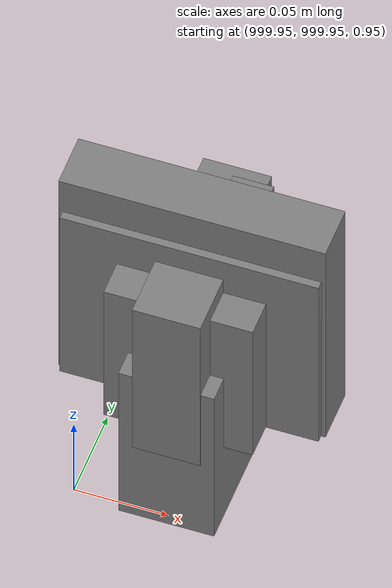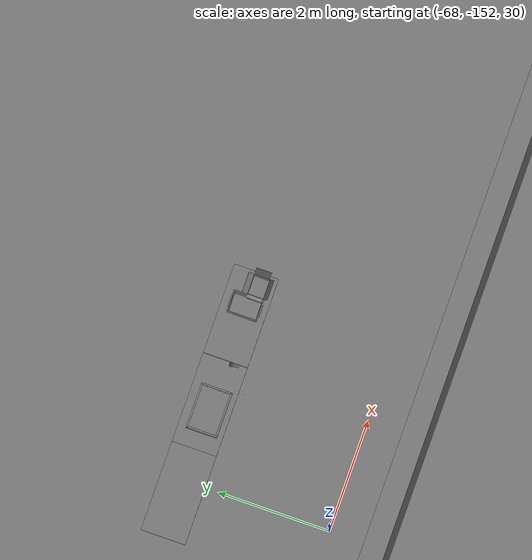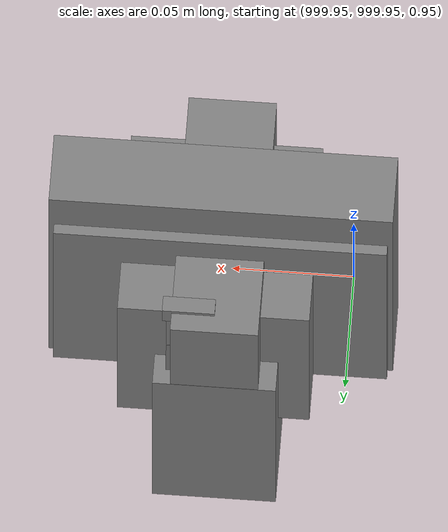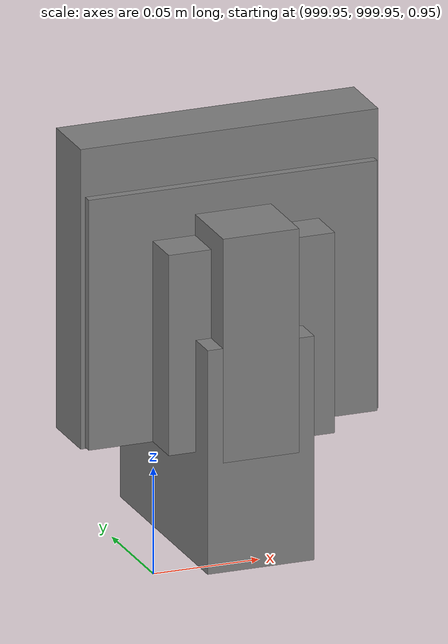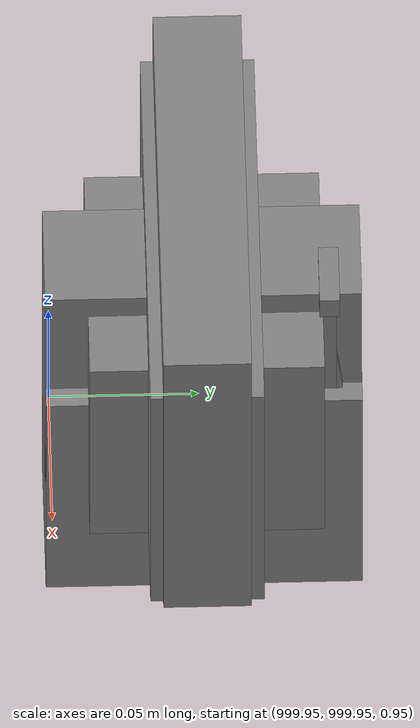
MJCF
<mujoco>
    <option gravity="0.000000000 0.000000000 -9.810000420" timestep="0.0049999999" integrator="implicitfast" density="1.225" viscosity="1.8000001e-05" noslip_iterations="10" iterations="100" sdf_iterations="50">
        <flag multiccd="disable"/>
    </option>
    <size memory="1000M"/>
    <compiler coordinate="local"/>
    <worldbody>
        <light cutoff="30" pos="0 1 1" dir="0 -1 -2"/>
        <light cutoff="30" pos="0 -1 1" dir="0 1 -2"/>
        <body pos="1000.000000000 1000.000000000 1.000000000" euler="0.000000000 0.000000000 180.000000000" name="openloong_gripper_2f85_fix_base_usda_wifi_box">
            <geom contype="1" conaffinity="1" density="1000" type="box" material="" rgba="0.500000000 0.500000000 0.500000000 1.000000000" solimp="0.899999976 0.949999988 0.001000000" friction="1.000000000 0.005000000 0.000100000" solref="0.020000000 1.000000000" margin="0" condim="3" group="0" pos="0.000000000 0.000000000 0.058978677" quat="0.000000000 0.000000047 0.000000000 1.000000000" size="0.068499997 0.018999999 0.059000000" name="openloong_gripper_2f85_fix_base_usda_geom_CCAAFBA3_45DF_483E_85A8_BB1EC088933F"/>
            <freejoint name="openloong_gripper_2f85_fix_base_usda_wifi_box_joint"/>
            <site size="0.005000000 0.005000000 0.005000000" rgba="0.500000000 0.500000000 0.500000000 1.000000000" pos="0.000000000 0.000000000 0.000000000" quat="0.999961913 0.008726500 0.000000000 0.000000000" group="0" type="sphere" name="openloong_gripper_2f85_fix_base_usda_wifi_boxsite"/>
        </body>
        <body pos="1000.000000000 1000.000000000 1.000000000" euler="0.000011953 0.000005123 -179.999984741" name="openloong_gripper_2f85_fix_base_usda_intel_box">
            <geom contype="1" conaffinity="1" density="1000" type="box" material="" rgba="0.500000000 0.500000000 0.500000000 1.000000000" solimp="0.899999976 0.949999988 0.001000000" friction="1.000000000 0.005000000 0.000100000" solref="0.020000000 1.000000000" margin="0" condim="3" group="0" pos="0.000000000 -0.000067139 0.000082284" quat="0.707106709 0.000000225 0.000000253 0.707106650" size="0.052800003 0.025300000 0.052800003" name="openloong_gripper_2f85_fix_base_usda_geom_12C5401B_A379_486E_9248_FF03EF1084F2"/>
            <freejoint name="openloong_gripper_2f85_fix_base_usda_intel_box_joint"/>
            <site size="0.005000000 0.005000000 0.005000000" rgba="0.500000000 0.500000000 0.500000000 1.000000000" pos="0.000000000 0.000000000 0.000000000" quat="0.999961913 0.008726500 0.000000000 0.000000000" group="0" type="sphere" name="openloong_gripper_2f85_fix_base_usda_intel_boxsite"/>
        </body>
        <body pos="-66.368698120 -148.948623657 31.166280746" euler="-84.126045227 -12.138069153 -154.547561646" mocap="true" name="spotlight1_SpotLight"/>
        <body pos="1000.000000000 999.999938965 1.000000000" euler="0.000000000 0.000000000 180.000000000" name="openloong_gripper_2f85_fix_base_usda_intelcore_i5">
            <geom contype="1" conaffinity="1" density="1000" type="box" material="" rgba="0.500000000 0.500000000 0.500000000 1.000000000" solimp="0.899999976 0.949999988 0.001000000" friction="1.000000000 0.005000000 0.000100000" solref="0.020000000 1.000000000" margin="0" condim="3" group="0" pos="0.000000000 0.000000000 0.051722717" quat="0.707106709 0.000000000 0.000000000 -0.707106769" size="0.052800000 0.018080002 0.052800000" name="openloong_gripper_2f85_fix_base_usda_geom_FF670963_9962_468B_9AEE_2827C086EB44"/>
            <freejoint name="openloong_gripper_2f85_fix_base_usda_intelcore_i5_joint"/>
            <site size="0.005000000 0.005000000 0.005000000" rgba="0.500000000 0.500000000 0.500000000 1.000000000" pos="0.000000000 0.000000000 0.000000000" quat="0.999961913 0.008726534 0.000000000 0.000000000" group="0" type="sphere" name="openloong_gripper_2f85_fix_base_usda_intelcore_i5site"/>
        </body>
        <body pos="-66.129379272 -149.767776489 31.170490265" euler="-53.820438385 25.671796799 171.118652344" mocap="true" name="spotlight6_SpotLight"/>
        <body pos="1000.000000000 1000.000000000 1.000000000" euler="0.000000000 0.000000000 180.000000000" name="openloong_gripper_2f85_fix_base_usda_cpu_fan">
            <geom contype="1" conaffinity="1" density="1000" type="box" material="" rgba="0.500000000 0.500000000 0.500000000 1.000000000" solimp="0.899999976 0.949999988 0.001000000" friction="1.000000000 0.005000000 0.000100000" solref="0.020000000 1.000000000" margin="0" condim="3" group="0" pos="0.000000000 0.000000000 0.070034981" quat="0.000000000 0.000000000 0.000000000 1.000000000" size="0.070700005 0.014699999 0.070700005" name="openloong_gripper_2f85_fix_base_usda_geom_00439152_3A9E_4C5F_B04C_FED9B0C666AC"/>
            <freejoint name="openloong_gripper_2f85_fix_base_usda_cpu_fan_joint"/>
            <site size="0.005000000 0.005000000 0.005000000" rgba="0.500000000 0.500000000 0.500000000 1.000000000" pos="0.000000000 0.000000000 0.000000000" quat="0.999961913 0.008726535 0.000000000 0.000000000" group="0" type="sphere" name="openloong_gripper_2f85_fix_base_usda_cpu_fancsite"/>
        </body>
        <body pos="-66.305587769 -149.647827148 31.167699814" euler="-168.840911865 4.090507507 99.631713867" mocap="true" name="spotlight3_SpotLight"/>
        <body pos="1000.000000000 1000.000000000 1.000000000" euler="0.000000000 0.000000000 180.000000000" name="openloong_gripper_2f85_fix_base_usda_battery_01">
            <geom contype="1" conaffinity="1" density="1000" type="box" material="" rgba="0.500000000 0.500000000 0.500000000 1.000000000" solimp="0.899999976 0.949999988 0.001000000" friction="1.000000000 0.005000000 0.000100000" solref="0.020000000 1.000000000" margin="0" condim="3" group="0" pos="-0.011123657 -0.041940309 0.101691343" quat="1.000000000 0.000000000 0.000000000 0.000000000" size="0.010800000 0.003375000 0.004725000" name="openloong_gripper_2f85_fix_base_usda_geom_0585567F_A787_4E21_BDD9_4E001F749C3B"/>
            <geom contype="1" conaffinity="1" density="1000" type="box" material="" rgba="0.500000000 0.500000000 0.500000000 1.000000000" solimp="0.899999976 0.949999988 0.001000000" friction="1.000000000 0.005000000 0.000100000" solref="0.020000000 1.000000000" margin="0" condim="3" group="0" pos="-0.010876465 -0.044247437 0.047066893" quat="0.998702705 -0.050920475 0.000000000 0.000000000" size="0.009450001 0.002700000 0.024975000" name="openloong_gripper_2f85_fix_base_usda_geom_B596E991_BDC8_45DF_B793_415FC294BA66"/>
            <geom contype="1" conaffinity="1" density="1000" type="box" material="" rgba="0.500000000 0.500000000 0.500000000 1.000000000" solimp="0.899999976 0.949999988 0.001000000" friction="1.000000000 0.005000000 0.000100000" solref="0.020000000 1.000000000" margin="0" condim="3" group="0" pos="-0.001235962 -0.000659180 0.047381196" quat="1.000000000 0.000000000 0.000000000 0.000000000" size="0.039420001 0.039150000 0.047250003" name="openloong_gripper_2f85_fix_base_usda_geom_E0F213BD_0E1A_4262_90D1_6650AE39C18E"/>
            <geom contype="1" conaffinity="1" density="1000" type="box" material="" rgba="0.500000000 0.500000000 0.500000000 1.000000000" solimp="0.899999976 0.949999988 0.001000000" friction="1.000000000 0.005000000 0.000100000" solref="0.020000000 1.000000000" margin="0" condim="3" group="0" pos="-0.010876465 -0.039138794 0.009851727" quat="1.000000000 0.000000000 0.000000000 0.000000000" size="0.009450001 0.010800000 0.013500000" name="openloong_gripper_2f85_fix_base_usda_geom_5A836812_B763_4E68_839D_EAFA773CAEC1"/>
            <geom contype="1" conaffinity="1" density="1000" type="box" material="" rgba="0.500000000 0.500000000 0.500000000 1.000000000" solimp="0.899999976 0.949999988 0.001000000" friction="1.000000000 0.005000000 0.000100000" solref="0.020000000 1.000000000" margin="0" condim="3" group="0" pos="-0.010876465 -0.041528322 0.071508206" quat="1.000000000 0.000000000 0.000000000 0.000000000" size="0.009450001 0.002700000 0.027000001" name="openloong_gripper_2f85_fix_base_usda_geom_CA2D4F06_CE2F_4454_AA85_ADBB6EEFA6E8"/>
            <freejoint name="openloong_gripper_2f85_fix_base_usda_battery_01_joint"/>
            <site size="0.005000000 0.005000000 0.005000000" rgba="0.500000000 0.500000000 0.500000000 1.000000000" pos="0.000000000 0.000000000 0.000000000" quat="0.999961913 0.008726500 0.000000000 0.000000000" group="0" type="sphere" name="openloong_gripper_2f85_fix_base_usda_battery_01site"/>
        </body>
        <body pos="-64.866622925 -149.383972168 30.183746338" euler="89.999984741 89.999946594 0.000000000" name="openloong_gripper_2f85_fix_base_usda_bluebox_01">
            <geom contype="1" conaffinity="1" density="1000" type="box" material="" rgba="0.500000000 0.500000000 0.500000000 1.000000000" solimp="0.899999976 0.949999988 0.001000000" friction="1.000000000 0.005000000 0.000100000" solref="0.020000000 1.000000000" margin="0" condim="3" group="0" pos="0.276580811 0.187225342 0.000068665" quat="0.707106948 0.000077471 0.707106352 0.000077486" size="0.100000001 0.057999998 0.010000000" name="openloong_gripper_2f85_fix_base_usda_geom_0188ECA4_CCDD_4114_9452_3203898BB115"/>
            <geom contype="1" conaffinity="1" density="1000" type="box" material="" rgba="0.500000000 0.500000000 0.500000000 1.000000000" solimp="0.899999976 0.949999988 0.001000000" friction="1.000000000 0.005000000 0.000100000" solref="0.020000000 1.000000000" margin="0" condim="3" group="0" pos="0.000000000 0.002883911 0.000000000" quat="0.999999881 0.000000000 0.000000000 0.000000000" size="0.254000008 0.003000000 0.172000006" name="openloong_gripper_2f85_fix_base_usda_geom_25C91AE7_6078_43CC_8188_E4522A6B887B"/>
            <geom contype="1" conaffinity="1" density="1000" type="box" material="" rgba="0.500000000 0.500000000 0.500000000 1.000000000" solimp="0.899999976 0.949999988 0.001000000" friction="1.000000000 0.005000000 0.000100000" solref="0.020000000 1.000000000" margin="0" condim="3" group="0" pos="0.000000000 0.124874115 0.173484802" quat="0.999796331 0.020176515 -0.000000015 0.000000030" size="0.259999990 0.119999997 0.007000000" name="openloong_gripper_2f85_fix_base_usda_geom_24DFDA65_144C_4F36_9150_7302B5129BB6"/>
            <geom contype="1" conaffinity="1" density="1000" type="box" material="" rgba="0.500000000 0.500000000 0.500000000 1.000000000" solimp="0.899999976 0.949999988 0.001000000" friction="1.000000000 0.005000000 0.000100000" solref="0.020000000 1.000000000" margin="0" condim="3" group="0" pos="0.000000000 0.124874115 -0.173469543" quat="0.999796331 -0.020176545 -0.000000015 0.000000000" size="0.259999990 0.119999997 0.007000000" name="openloong_gripper_2f85_fix_base_usda_geom_7D0D4715_7CC8_4EE7_B893_AE463FBDFCE5"/>
            <geom contype="1" conaffinity="1" density="1000" type="box" material="" rgba="0.500000000 0.500000000 0.500000000 1.000000000" solimp="0.899999976 0.949999988 0.001000000" friction="1.000000000 0.005000000 0.000100000" solref="0.020000000 1.000000000" margin="0" condim="3" group="0" pos="0.000000000 0.214008331 0.188980103" quat="0.999912977 0.013176724 0.000000015 0.000000000" size="0.259999990 0.029999999 0.012500000" name="openloong_gripper_2f85_fix_base_usda_geom_652B2E86_197A_4E78_B6E8_2C985A7E746E"/>
            <geom contype="1" conaffinity="1" density="1000" type="box" material="" rgba="0.500000000 0.500000000 0.500000000 1.000000000" solimp="0.899999976 0.949999988 0.001000000" friction="1.000000000 0.005000000 0.000100000" solref="0.020000000 1.000000000" margin="0" condim="3" group="0" pos="-0.258361816 0.125289917 0.001876831" quat="0.702796936 -0.020792112 0.710783124 0.020769298" size="0.189999998 0.119999997 0.009000000" name="openloong_gripper_2f85_fix_base_usda_geom_CE5E9457_8E83_4CCF_9F1B_716D28C747C3"/>
            <geom contype="1" conaffinity="1" density="1000" type="box" material="" rgba="0.500000000 0.500000000 0.500000000 1.000000000" solimp="0.899999976 0.949999988 0.001000000" friction="1.000000000 0.005000000 0.000100000" solref="0.020000000 1.000000000" margin="0" condim="3" group="0" pos="0.000000000 0.214008331 -0.188980103" quat="0.999912977 -0.013176769 0.000000030 0.000000015" size="0.259999990 0.029999999 0.012500000" name="openloong_gripper_2f85_fix_base_usda_geom_EA1D99CD_96E8_4FF2_BFC3_D7B0B7B2D198"/>
            <geom contype="1" conaffinity="1" density="1000" type="box" material="" rgba="0.500000000 0.500000000 0.500000000 1.000000000" solimp="0.899999976 0.949999988 0.001000000" friction="1.000000000 0.005000000 0.000100000" solref="0.020000000 1.000000000" margin="0" condim="3" group="0" pos="-0.276611328 0.187225342 0.000068665" quat="0.707106650 0.000077441 0.707106709 0.000077456" size="0.100000001 0.057999998 0.010000000" name="openloong_gripper_2f85_fix_base_usda_geom_E4673B15_7650_426F_8A07_1A910D45BFB5"/>
            <geom contype="1" conaffinity="1" density="1000" type="box" material="" rgba="0.500000000 0.500000000 0.500000000 1.000000000" solimp="0.899999976 0.949999988 0.001000000" friction="1.000000000 0.005000000 0.000100000" solref="0.020000000 1.000000000" margin="0" condim="3" group="0" pos="0.258331299 0.125289917 0.001876831" quat="0.702851415 0.018856421 0.710823774 -0.019329369" size="0.189999998 0.119999997 0.009000000" name="openloong_gripper_2f85_fix_base_usda_geom_4EAFEBA9_1E19_4C73_9A17_569821E195D7"/>
            <freejoint name="openloong_gripper_2f85_fix_base_usda_bluebox_01_joint"/>
            <site size="0.005000000 0.005000000 0.005000000" rgba="0.500000000 0.500000000 0.500000000 1.000000000" pos="0.000000000 0.000000000 0.000000000" quat="0.999961913 0.008726534 0.000000000 0.000000000" group="0" type="sphere" name="openloong_gripper_2f85_fix_base_usda_bluebox_01site"/>
        </body>
        <body pos="-64.496299744 -149.491867065 30.235729218" euler="0.000000000 0.000000000 89.999946594" name="openloong_gripper_2f85_fix_base_usda_cardboardbox_01">
            <geom contype="1" conaffinity="1" density="1000" type="box" material="" rgba="0.500000000 0.500000000 0.500000000 1.000000000" solimp="0.899999976 0.949999988 0.001000000" friction="1.000000000 0.005000000 0.000100000" solref="0.020000000 1.000000000" margin="0" condim="3" group="0" pos="-0.003166199 -0.004086494 0.005052090" quat="1.000000000 0.000000000 0.000000000 0.000000000" size="0.142499998 0.177500010 0.005000000" name="openloong_gripper_2f85_fix_base_usda_geom_98384F63_20EB_478A_BA13_03E5C3838DE4"/>
            <geom contype="1" conaffinity="1" density="1000" type="box" material="" rgba="0.500000000 0.500000000 0.500000000 1.000000000" solimp="0.899999976 0.949999988 0.001000000" friction="1.000000000 0.005000000 0.000100000" solref="0.020000000 1.000000000" margin="0" condim="3" group="0" pos="-0.003166199 0.170316696 0.150570869" quat="1.000000000 0.000000000 0.000000000 0.000000000" size="0.142499998 0.005000000 0.149999991" name="openloong_gripper_2f85_fix_base_usda_geom_5F6EA5F5_5E47_41AE_883C_95A5C500EC6C"/>
            <geom contype="1" conaffinity="1" density="1000" type="box" material="" rgba="0.500000000 0.500000000 0.500000000 1.000000000" solimp="0.899999976 0.949999988 0.001000000" friction="1.000000000 0.005000000 0.000100000" solref="0.020000000 1.000000000" margin="0" condim="3" group="0" pos="-0.147399902 -0.005307198 0.150570869" quat="1.000000000 0.000000000 0.000000000 0.000000000" size="0.005000000 0.177500010 0.149999991" name="openloong_gripper_2f85_fix_base_usda_geom_1E61485A_0D55_4347_975F_5A90378018C9"/>
            <geom contype="1" conaffinity="1" density="1000" type="box" material="" rgba="0.500000000 0.500000000 0.500000000 1.000000000" solimp="0.899999976 0.949999988 0.001000000" friction="1.000000000 0.005000000 0.000100000" solref="0.020000000 1.000000000" margin="0" condim="3" group="0" pos="0.140275955 -0.005307198 0.150570869" quat="1.000000000 0.000000000 0.000000000 0.000000000" size="0.005000000 0.177500010 0.149999991" name="openloong_gripper_2f85_fix_base_usda_geom_33A26FFC_76C8_4F76_BBF6_0B8F9D384740"/>
            <geom contype="1" conaffinity="1" density="1000" type="box" material="" rgba="0.500000000 0.500000000 0.500000000 1.000000000" solimp="0.899999976 0.949999988 0.001000000" friction="1.000000000 0.005000000 0.000100000" solref="0.020000000 1.000000000" margin="0" condim="3" group="0" pos="-0.003166199 -0.181550980 0.150570869" quat="1.000000000 0.000000000 0.000000000 0.000000000" size="0.142499998 0.005000000 0.149999991" name="openloong_gripper_2f85_fix_base_usda_geom_86381E1A_657B_4470_A25A_0B8802BA0226"/>
            <freejoint name="openloong_gripper_2f85_fix_base_usda_cardboardbox_01_joint"/>
            <site size="0.005000000 0.005000000 0.005000000" rgba="0.500000000 0.500000000 0.500000000 1.000000000" pos="0.000000000 0.000000000 0.000000000" quat="0.999961913 0.008726535 0.000000000 0.000000000" group="0" type="sphere" name="openloong_gripper_2f85_fix_base_usda_site_CCA86C14_2E50_4C04_9C62_57F8AA83FA10"/>
            <body pos="0.139160156 -0.004048347 0.301930904" euler="-179.999954224 49.383502960 179.999954224" name="openloong_gripper_2f85_fix_base_usda_A1_006">
                <geom contype="1" conaffinity="1" density="1000" type="box" material="" rgba="0.500000000 0.500000000 0.500000000 1.000000000" solimp="0.899999976 0.949999988 0.001000000" friction="1.000000000 0.005000000 0.000100000" solref="0.020000000 1.000000000" margin="0" condim="3" group="0" pos="-0.071587563 0.000009537 0.001745224" quat="0.999999881 0.000000000 0.000000000 0.000000000" size="0.071249999 0.179999992 0.002500000" name="openloong_gripper_2f85_fix_base_usda_geom_C5521819_38E0_436E_A559_AC8D2C63FB3C"/>
                <joint armature="0" stiffness="0.07" damping="0.0099999998" axis="0.000000 1.000000 0.000000" type="hinge" name="openloong_gripper_2f85_fix_base_usda_A1_006"/>
            </body>
            <body pos="-0.145902634 -0.004086494 0.301938057" euler="-180.000000000 -60.000011444 -180.000000000" name="openloong_gripper_2f85_fix_base_usda_A2_006">
                <geom contype="1" conaffinity="1" density="1000" type="box" material="" rgba="0.500000000 0.500000000 0.500000000 1.000000000" solimp="0.899999976 0.949999988 0.001000000" friction="1.000000000 0.005000000 0.000100000" solref="0.020000000 1.000000000" margin="0" condim="3" group="0" pos="0.071268082 0.000009537 0.002717972" quat="0.000002921 0.000000000 -0.000000030 0.999999881" size="0.071249999 0.179999992 0.002500000" name="openloong_gripper_2f85_fix_base_usda_geom_1628305E_2A10_4EC1_80AB_07B6D07517C1"/>
                <joint armature="0" stiffness="0.07" damping="0.0099999998" axis="0.000000 1.000000 0.000000" type="hinge" name="openloong_gripper_2f85_fix_base_usda_A2_006"/>
            </body>
            <body pos="-0.003385544 0.175991058 0.301930904" euler="-125.858116150 -0.000004561 0.000002331" name="openloong_gripper_2f85_fix_base_usda_B2_006">
                <geom contype="1" conaffinity="1" density="1000" type="box" material="" rgba="0.500000000 0.500000000 0.500000000 1.000000000" solimp="0.899999976 0.949999988 0.001000000" friction="1.000000000 0.005000000 0.000100000" solref="0.020000000 1.000000000" margin="0" condim="3" group="0" pos="0.000009537 -0.070939064 -0.002470016" quat="0.999614120 0.027776197 -0.000000015 0.000000030" size="0.137500003 0.064999998 0.005000000" name="openloong_gripper_2f85_fix_base_usda_geom_7135C9B7_53C8_446B_822A_F5A7E1DA76FD"/>
                <joint armature="0" stiffness="0.07" damping="0.0099999998" axis="1.000000 0.000000 0.000000" type="hinge" name="openloong_gripper_2f85_fix_base_usda_B2_006"/>
            </body>
            <body pos="-0.003385544 -0.184140205 0.301938057" euler="147.805557251 0.000000000 0.000000000" name="openloong_gripper_2f85_fix_base_usda_B1_006">
                <geom contype="1" conaffinity="1" density="1000" type="box" material="" rgba="0.500000000 0.500000000 0.500000000 1.000000000" solimp="0.899999976 0.949999988 0.001000000" friction="1.000000000 0.005000000 0.000100000" solref="0.020000000 1.000000000" margin="0" condim="3" group="0" pos="-0.000028610 0.070202351 -0.002703667" quat="0.999614179 -0.027776167 0.000000000 0.000000000" size="0.137500003 0.064999998 0.005000000" name="openloong_gripper_2f85_fix_base_usda_geom_E7A70BE0_5AF9_4B23_94F4_234968446E88"/>
                <joint armature="0" stiffness="0.07" damping="0.0099999998" axis="1.000000 0.000000 0.000000" type="hinge" name="openloong_gripper_2f85_fix_base_usda_B1_006"/>
            </body>
        </body>
        <body pos="-65.882858276 -149.481979370 30.229999542" euler="-64.487716675 0.000000000 0.000000000" name="openloong_gripper_2f85_fix_base_usda_Barcode">
            <geom contype="1" conaffinity="1" density="1000" type="box" material="" rgba="0.500000000 0.500000000 0.500000000 1.000000000" solimp="0.899999976 0.949999988 0.001000000" friction="1.000000000 0.005000000 0.000100000" solref="0.020000000 1.000000000" margin="0" condim="3" group="0" pos="0.000000000 0.013038635 0.001419067" quat="0.000000000 0.000000000 0.000000000 1.000000119" size="0.034000002 0.010000000 0.017999999" name="openloong_gripper_2f85_fix_base_usda_geom_DE59922E_7190_4501_9D2E_4C1F123F3D4A"/>
            <geom contype="1" conaffinity="1" density="1000" type="box" material="" rgba="0.500000000 0.500000000 0.500000000 1.000000000" solimp="0.899999976 0.949999988 0.001000000" friction="1.000000000 0.005000000 0.000100000" solref="0.020000000 1.000000000" margin="0" condim="3" group="0" pos="0.000000000 -0.035301208 -0.007095337" quat="0.000000000 0.000000000 -0.043619365 0.999048233" size="0.028999999 0.010000000 0.020000000" name="openloong_gripper_2f85_fix_base_usda_geom_755052BD_1905_4505_A6B9_791E1DB2AB29"/>
            <geom contype="1" conaffinity="1" density="1000" type="box" material="" rgba="0.500000000 0.500000000 0.500000000 1.000000000" solimp="0.899999976 0.949999988 0.001000000" friction="1.000000000 0.005000000 0.000100000" solref="0.020000000 1.000000000" margin="0" condim="3" group="0" pos="0.000000000 -0.043411255 -0.011749268" quat="0.922262907 0.386563420 0.000000000 0.000000000" size="0.026000001 0.010000000 0.020000000" name="openloong_gripper_2f85_fix_base_usda_geom_6C215B21_250B_4296_8022_F74F928F13C8"/>
            <geom contype="1" conaffinity="1" density="1000" type="box" material="" rgba="0.500000000 0.500000000 0.500000000 1.000000000" solimp="0.899999976 0.949999988 0.001000000" friction="1.000000000 0.005000000 0.000100000" solref="0.020000000 1.000000000" margin="0" condim="3" group="0" pos="0.000000000 -0.016967773 -0.031860352" quat="0.000000000 0.000000000 0.000000000 1.000000119" size="0.008000000 0.010000000 0.013000000" name="openloong_gripper_2f85_fix_base_usda_geom_C42FD783_24FE_4416_AE91_B16E0BAC9F24"/>
            <geom contype="1" conaffinity="1" density="1000" type="box" material="" rgba="0.500000000 0.500000000 0.500000000 1.000000000" solimp="0.899999976 0.949999988 0.001000000" friction="1.000000000 0.005000000 0.000100000" solref="0.020000000 1.000000000" margin="0" condim="3" group="0" pos="0.000000000 -0.001869202 0.000312805" quat="0.953716993 0.300705761 0.000000000 0.000000000" size="0.032000002 0.010000000 0.018999999" name="openloong_gripper_2f85_fix_base_usda_geom_4A2C3AED_86E0_42A8_A63C_3B306BEF597B"/>
            <geom contype="1" conaffinity="1" density="1000" type="box" material="" rgba="0.500000000 0.500000000 0.500000000 1.000000000" solimp="0.899999976 0.949999988 0.001000000" friction="1.000000000 0.005000000 0.000100000" solref="0.020000000 1.000000000" margin="0" condim="3" group="0" pos="0.000000000 -0.019531250 -0.003173828" quat="0.953716993 0.300705761 0.000000000 0.000000000" size="0.030999999 0.010000000 0.020000000" name="openloong_gripper_2f85_fix_base_usda_geom_4CC9EC99_D1CC_435E_B19B_3B43F27861F8"/>
            <geom contype="1" conaffinity="1" density="1000" type="box" material="" rgba="0.500000000 0.500000000 0.500000000 1.000000000" solimp="0.899999976 0.949999988 0.001000000" friction="1.000000000 0.005000000 0.000100000" solref="0.020000000 1.000000000" margin="0" condim="3" group="0" pos="0.000000000 -0.035301208 -0.007095337" quat="0.953716993 0.300705761 0.000000000 0.000000000" size="0.028999999 0.010000000 0.020000000" name="openloong_gripper_2f85_fix_base_usda_geom_F6412EC2_B9CC_4D73_A4C5_0E920601C7C8"/>
            <geom contype="1" conaffinity="1" density="1000" type="box" material="" rgba="0.500000000 0.500000000 0.500000000 1.000000000" solimp="0.899999976 0.949999988 0.001000000" friction="1.000000000 0.005000000 0.000100000" solref="0.020000000 1.000000000" margin="0" condim="3" group="0" pos="0.000000000 -0.042617798 -0.071121216" quat="0.000000000 0.000000000 0.000000000 1.000000119" size="0.013000000 0.021000000 0.059999999" name="openloong_gripper_2f85_fix_base_usda_geom_F0DD9466_C730_47A7_8D79_0E73327C821D"/>
            <freejoint name="openloong_gripper_2f85_fix_base_usda_Barcode_joint"/>
            <site size="0.005000000 0.005000000 0.005000000" rgba="0.500000000 0.500000000 0.500000000 1.000000000" pos="0.000000000 0.000000000 0.000000000" quat="1.000000000 0.000000000 0.000000000 0.000000000" group="0" type="sphere" name="openloong_gripper_2f85_fix_base_usda_Barcode_site"/>
        </body>
        <body pos="-66.745018005 -149.392349243 30.184000015" euler="0.000000000 0.000000000 89.999946594" name="[22329726031854]_Basket_01">
            <geom contype="1" conaffinity="1" density="1000" type="box" material="" rgba="0.500000000 0.500000000 0.500000000 1.000000000" solimp="0.899999976 0.949999988 0.001000000" friction="1.000000000 0.005000000 0.000100000" solref="0.020000000 1.000000000" margin="0" condim="3" group="0" pos="-0.052425385 0.389207840 0.089787483" quat="0.707107008 0.000000000 0.000000000 0.707106411" size="0.014249999 0.014249999 0.059999999" name="[22329726031854]_geom_451242C3_F21C_49CC_BC3A_A49EF0DF7788"/>
            <geom contype="1" conaffinity="1" density="1000" type="box" material="" rgba="0.500000000 0.500000000 0.500000000 1.000000000" solimp="0.899999976 0.949999988 0.001000000" friction="1.000000000 0.005000000 0.000100000" solref="0.020000000 1.000000000" margin="0" condim="3" group="0" pos="0.264015198 -0.133043289 0.089787483" quat="0.707107008 0.000000000 0.000000000 0.707106411" size="0.014249999 0.014249999 0.059999999" name="[22329726031854]_geom_1E158C1F_F6F1_4C20_8868_62E027657569"/>
            <geom contype="1" conaffinity="1" density="1000" type="box" material="" rgba="0.500000000 0.500000000 0.500000000 1.000000000" solimp="0.899999976 0.949999988 0.001000000" friction="1.000000000 0.005000000 0.000100000" solref="0.020000000 1.000000000" margin="0" condim="3" group="0" pos="-0.264015198 -0.265548706 0.089793205" quat="0.707107008 0.000000000 0.000000000 0.707106411" size="0.014249999 0.014249999 0.059999999" name="[22329726031854]_geom_E829CED4_883D_48F8_9BA5_218D424442E5"/>
            <geom contype="1" conaffinity="1" density="1000" type="box" material="" rgba="0.500000000 0.500000000 0.500000000 1.000000000" solimp="0.899999976 0.949999988 0.001000000" friction="1.000000000 0.005000000 0.000100000" solref="0.020000000 1.000000000" margin="0" condim="3" group="0" pos="-0.160263062 -0.389322281 0.089793205" quat="0.707107008 0.000000000 0.000000000 0.707106411" size="0.014249999 0.014249999 0.059999999" name="[22329726031854]_geom_60425F03_6C95_4203_8301_6F05BDF89FEE"/>
            <geom contype="1" conaffinity="1" density="1000" type="box" material="" rgba="0.500000000 0.500000000 0.500000000 1.000000000" solimp="0.899999976 0.949999988 0.001000000" friction="1.000000000 0.005000000 0.000100000" solref="0.020000000 1.000000000" margin="0" condim="3" group="0" pos="0.162265778 -0.389322281 0.089787483" quat="0.707107008 0.000000000 0.000000000 0.707106411" size="0.014249999 0.014249999 0.059999999" name="[22329726031854]_geom_28B93638_8F8C_46A2_B135_356C6819991E"/>
            <geom contype="1" conaffinity="1" density="1000" type="box" material="" rgba="0.500000000 0.500000000 0.500000000 1.000000000" solimp="0.899999976 0.949999988 0.001000000" friction="1.000000000 0.005000000 0.000100000" solref="0.020000000 1.000000000" margin="0" condim="3" group="0" pos="0.264015198 0.389207840 0.089787483" quat="0.707107008 0.000000000 0.000000000 0.707106411" size="0.014249999 0.014249999 0.059999999" name="[22329726031854]_geom_78D90281_7748_4FDC_B20D_F4FCF9B0C9F2"/>
            <geom contype="1" conaffinity="1" density="1000" type="box" material="" rgba="0.500000000 0.500000000 0.500000000 1.000000000" solimp="0.899999976 0.949999988 0.001000000" friction="1.000000000 0.005000000 0.000100000" solref="0.020000000 1.000000000" margin="0" condim="3" group="0" pos="-0.264015198 -0.133043289 0.089793205" quat="0.707107008 0.000000000 0.000000000 0.707106411" size="0.014249999 0.014249999 0.059999999" name="[22329726031854]_geom_7AC1D64D_867B_4F63_B692_762274591A1B"/>
            <geom contype="1" conaffinity="1" density="1000" type="box" material="" rgba="0.500000000 0.500000000 0.500000000 1.000000000" solimp="0.899999976 0.949999988 0.001000000" friction="1.000000000 0.005000000 0.000100000" solref="0.020000000 1.000000000" margin="0" condim="3" group="0" pos="-0.264026642 0.269256592 0.089793205" quat="0.707107008 0.000000000 0.000000000 0.707106411" size="0.014249999 0.014249999 0.059999999" name="[22329726031854]_geom_FFB66145_5575_4B1B_9B03_47D0AC14CFEA"/>
            <geom contype="1" conaffinity="1" density="1000" type="box" material="" rgba="0.500000000 0.500000000 0.500000000 1.000000000" solimp="0.899999976 0.949999988 0.001000000" friction="1.000000000 0.005000000 0.000100000" solref="0.020000000 1.000000000" margin="0" condim="3" group="0" pos="0.054462433 0.389207840 0.089787483" quat="0.707107008 0.000000000 0.000000000 0.707106411" size="0.014249999 0.014249999 0.059999999" name="[22329726031854]_geom_31B22085_D654_4D9E_8141_C17A3AAC430E"/>
            <geom contype="1" conaffinity="1" density="1000" type="box" material="" rgba="0.500000000 0.500000000 0.500000000 1.000000000" solimp="0.899999976 0.949999988 0.001000000" friction="1.000000000 0.005000000 0.000100000" solref="0.020000000 1.000000000" margin="0" condim="3" group="0" pos="0.054462433 -0.389322281 0.089787483" quat="0.707107008 0.000000000 0.000000000 0.707106411" size="0.014249999 0.014249999 0.059999999" name="[22329726031854]_geom_4C0AED42_D315_477D_B81D_4B94DC8DE88A"/>
            <geom contype="1" conaffinity="1" density="1000" type="box" material="" rgba="0.500000000 0.500000000 0.500000000 1.000000000" solimp="0.899999976 0.949999988 0.001000000" friction="1.000000000 0.005000000 0.000100000" solref="0.020000000 1.000000000" margin="0" condim="3" group="0" pos="0.264015198 0.269256592 0.089793205" quat="0.707107008 0.000000000 0.000000000 0.707106411" size="0.014249999 0.014249999 0.059999999" name="[22329726031854]_geom_737E1AC8_D70B_408C_ACEC_B6AB5E945907"/>
            <geom contype="1" conaffinity="1" density="1000" type="box" material="" rgba="0.500000000 0.500000000 0.500000000 1.000000000" solimp="0.899999976 0.949999988 0.001000000" friction="1.000000000 0.005000000 0.000100000" solref="0.020000000 1.000000000" margin="0" condim="3" group="0" pos="0.264015198 -0.389322281 0.089787483" quat="0.707107008 0.000000000 0.000000000 0.707106411" size="0.014249999 0.014249999 0.059999999" name="[22329726031854]_geom_DC7E59AA_4109_44F3_B989_6129A99DA59D"/>
            <geom contype="1" conaffinity="1" density="1000" type="box" material="" rgba="0.500000000 0.500000000 0.500000000 1.000000000" solimp="0.899999976 0.949999988 0.001000000" friction="1.000000000 0.005000000 0.000100000" solref="0.020000000 1.000000000" margin="0" condim="3" group="0" pos="0.000000000 0.000000000 0.015998840" quat="0.707107008 0.000000000 0.000000000 0.707106411" size="0.403499991 0.279000014 0.015750000" name="[22329726031854]_geom_EA8C1CB8_F8A5_41A2_ABF5_1487893794DC"/>
            <geom contype="1" conaffinity="1" density="1000" type="box" material="" rgba="0.500000000 0.500000000 0.500000000 1.000000000" solimp="0.899999976 0.949999988 0.001000000" friction="1.000000000 0.005000000 0.000100000" solref="0.020000000 1.000000000" margin="0" condim="3" group="0" pos="0.000000000 -0.389476776 0.163619041" quat="0.707107008 0.000000000 0.000000000 0.707106411" size="0.015000000 0.277500004 0.015750000" name="[22329726031854]_geom_117C044F_E4A6_413F_8EAA_548DB5E3FB28"/>
            <geom contype="1" conaffinity="1" density="1000" type="box" material="" rgba="0.500000000 0.500000000 0.500000000 1.000000000" solimp="0.899999976 0.949999988 0.001000000" friction="1.000000000 0.005000000 0.000100000" solref="0.020000000 1.000000000" margin="0" condim="3" group="0" pos="0.162265778 0.389207840 0.089787483" quat="0.707107008 0.000000000 0.000000000 0.707106411" size="0.014249999 0.014249999 0.059999999" name="[22329726031854]_geom_DF4FE20E_1116_42DC_B8FA_3E82F8449FD0"/>
            <geom contype="1" conaffinity="1" density="1000" type="box" material="" rgba="0.500000000 0.500000000 0.500000000 1.000000000" solimp="0.899999976 0.949999988 0.001000000" friction="1.000000000 0.005000000 0.000100000" solref="0.020000000 1.000000000" margin="0" condim="3" group="0" pos="0.000000000 0.389471054 0.163619041" quat="0.707107008 0.000000000 0.000000000 0.707106411" size="0.015000000 0.277500004 0.015750000" name="[22329726031854]_geom_BB0D439A_2F82_4EC4_A800_F5CC87044919"/>
            <geom contype="1" conaffinity="1" density="1000" type="box" material="" rgba="0.500000000 0.500000000 0.500000000 1.000000000" solimp="0.899999976 0.949999988 0.001000000" friction="1.000000000 0.005000000 0.000100000" solref="0.020000000 1.000000000" margin="0" condim="3" group="0" pos="-0.263511658 0.000000000 0.163619041" quat="0.707107008 0.000000000 0.000000000 0.707106411" size="0.403499991 0.015000000 0.015750000" name="[22329726031854]_geom_FBD70175_41E5_4FAA_A2FD_C42DC2A35B28"/>
            <geom contype="1" conaffinity="1" density="1000" type="box" material="" rgba="0.500000000 0.500000000 0.500000000 1.000000000" solimp="0.899999976 0.949999988 0.001000000" friction="1.000000000 0.005000000 0.000100000" solref="0.020000000 1.000000000" margin="0" condim="3" group="0" pos="-0.264015198 0.141334534 0.089793205" quat="0.707107008 0.000000000 0.000000000 0.707106411" size="0.014249999 0.014249999 0.059999999" name="[22329726031854]_geom_BA78A2EA_7194_4E34_BBC9_B2A6EAD7FB25"/>
            <geom contype="1" conaffinity="1" density="1000" type="box" material="" rgba="0.500000000 0.500000000 0.500000000 1.000000000" solimp="0.899999976 0.949999988 0.001000000" friction="1.000000000 0.005000000 0.000100000" solref="0.020000000 1.000000000" margin="0" condim="3" group="0" pos="0.264015198 -0.265548706 0.089787483" quat="0.707107008 0.000000000 0.000000000 0.707106411" size="0.014249999 0.014249999 0.059999999" name="[22329726031854]_geom_F62C31B6_5007_4A40_8204_571ADA941139"/>
            <geom contype="1" conaffinity="1" density="1000" type="box" material="" rgba="0.500000000 0.500000000 0.500000000 1.000000000" solimp="0.899999976 0.949999988 0.001000000" friction="1.000000000 0.005000000 0.000100000" solref="0.020000000 1.000000000" margin="0" condim="3" group="0" pos="-0.160263062 0.389207840 0.089787483" quat="0.707107008 0.000000000 0.000000000 0.707106411" size="0.014249999 0.014249999 0.059999999" name="[22329726031854]_geom_ED8BF223_6A9A_4BE1_B103_27621EB67258"/>
            <geom contype="1" conaffinity="1" density="1000" type="box" material="" rgba="0.500000000 0.500000000 0.500000000 1.000000000" solimp="0.899999976 0.949999988 0.001000000" friction="1.000000000 0.005000000 0.000100000" solref="0.020000000 1.000000000" margin="0" condim="3" group="0" pos="-0.052425385 -0.389322281 0.089787483" quat="0.707107008 0.000000000 0.000000000 0.707106411" size="0.014249999 0.014249999 0.059999999" name="[22329726031854]_geom_14C13033_2E35_4C29_AE3E_4C8FFB5518A5"/>
            <geom contype="1" conaffinity="1" density="1000" type="box" material="" rgba="0.500000000 0.500000000 0.500000000 1.000000000" solimp="0.899999976 0.949999988 0.001000000" friction="1.000000000 0.005000000 0.000100000" solref="0.020000000 1.000000000" margin="0" condim="3" group="0" pos="-0.264026642 -0.389322281 0.089793205" quat="0.707107008 0.000000000 0.000000000 0.707106411" size="0.014249999 0.014249999 0.059999999" name="[22329726031854]_geom_BDC4F6E9_9C24_4BD4_82D0_1F186F718A82"/>
            <geom contype="1" conaffinity="1" density="1000" type="box" material="" rgba="0.500000000 0.500000000 0.500000000 1.000000000" solimp="0.899999976 0.949999988 0.001000000" friction="1.000000000 0.005000000 0.000100000" solref="0.020000000 1.000000000" margin="0" condim="3" group="0" pos="0.264015198 0.141334534 0.089787483" quat="0.707107008 0.000000000 0.000000000 0.707106411" size="0.014249999 0.014249999 0.059999999" name="[22329726031854]_geom_365BC0B1_16A7_4E3E_824E_9BC368AF86FF"/>
            <geom contype="1" conaffinity="1" density="1000" type="box" material="" rgba="0.500000000 0.500000000 0.500000000 1.000000000" solimp="0.899999976 0.949999988 0.001000000" friction="1.000000000 0.005000000 0.000100000" solref="0.020000000 1.000000000" margin="0" condim="3" group="0" pos="-0.264015198 0.389207840 0.089793205" quat="0.707107008 0.000000000 0.000000000 0.707106411" size="0.014249999 0.014249999 0.059999999" name="[22329726031854]_geom_CD88F9BC_12AB_479D_8A2A_B9FC27D033E2"/>
            <geom contype="1" conaffinity="1" density="1000" type="box" material="" rgba="0.500000000 0.500000000 0.500000000 1.000000000" solimp="0.899999976 0.949999988 0.001000000" friction="1.000000000 0.005000000 0.000100000" solref="0.020000000 1.000000000" margin="0" condim="3" group="0" pos="0.264015198 0.004480362 0.089787483" quat="0.707107008 0.000000000 0.000000000 0.707106411" size="0.014249999 0.014249999 0.059999999" name="[22329726031854]_geom_A193CFDB_AF7F_4E1D_B570_1B674658535B"/>
            <geom contype="1" conaffinity="1" density="1000" type="box" material="" rgba="0.500000000 0.500000000 0.500000000 1.000000000" solimp="0.899999976 0.949999988 0.001000000" friction="1.000000000 0.005000000 0.000100000" solref="0.020000000 1.000000000" margin="0" condim="3" group="0" pos="0.263694763 -0.000011444 0.163619041" quat="0.707107008 0.000000000 0.000000000 0.707106411" size="0.403499991 0.015000000 0.015750000" name="[22329726031854]_geom_8AAA8E5E_36C2_41E2_8B8E_26349CD16930"/>
            <geom contype="1" conaffinity="1" density="1000" type="box" material="" rgba="0.500000000 0.500000000 0.500000000 1.000000000" solimp="0.899999976 0.949999988 0.001000000" friction="1.000000000 0.005000000 0.000100000" solref="0.020000000 1.000000000" margin="0" condim="3" group="0" pos="-0.264015198 0.004480362 0.089793205" quat="0.707107008 0.000000000 0.000000000 0.707106411" size="0.014249999 0.014249999 0.059999999" name="[22329726031854]_geom_3F50AAB9_E777_4471_A222_B69BEDEB14AD"/>
            <freejoint name="[22329726031854]_joint_96B9DAC4_E472_4891_93AA_A7B2478EBFE1"/>
        </body>
        <body pos="0.000000000 0.000000000 0.000000000" euler="0.000000000 0.000000000 0.000000000" name="Static Objects_Static Objects">
            <geom contype="1" conaffinity="1" density="1000" type="box" material="" rgba="0.500000000 0.500000000 0.500000000 1.000000000" solimp="0.899999976 0.949999988 0.001000000" friction="1.000000000 0.005000000 0.000100000" solref="0.020000000 1.000000000" margin="0" condim="3" group="0" pos="-67.544113159 -149.365814209 29.727830887" quat="0.500000417 0.499999970 0.499999553 0.499999970" size="0.381000012 0.319999993 0.041000001" name="Static Objects_geom_92CC3632_1DEB_4655_A0E1_FFDA2F02596C"/>
            <geom contype="1" conaffinity="1" density="1000" type="box" material="" rgba="0.500000000 0.500000000 0.500000000 1.000000000" solimp="0.899999976 0.949999988 0.001000000" friction="1.000000000 0.005000000 0.000100000" solref="0.020000000 1.000000000" margin="0" condim="3" group="0" pos="-68.239501953 -149.365814209 30.086868286" quat="0.500000417 0.499999970 0.499999553 0.499999970" size="0.370999992 0.039500002 0.745000005" name="Static Objects_geom_5C6AD4A3_5D2F_43C6_AD15_8C4E989F08B8"/>
            <geom contype="1" conaffinity="1" density="1000" type="box" material="" rgba="0.500000000 0.500000000 0.500000000 1.000000000" solimp="0.899999976 0.949999988 0.001000000" friction="1.000000000 0.005000000 0.000100000" solref="0.020000000 1.000000000" margin="0" condim="3" group="0" pos="-68.239501953 -149.365814209 30.147235870" quat="0.500000417 0.499999970 0.499999553 0.499999970" size="0.400000006 0.022000000 0.800000012" name="Static Objects_geom_CDF46C6B_1DB0_4C6D_AF5E_25750F995F5B"/>
            <geom contype="1" conaffinity="1" density="1000" type="box" material="" rgba="0.500000000 0.500000000 0.500000000 1.000000000" solimp="0.899999976 0.949999988 0.001000000" friction="1.000000000 0.005000000 0.000100000" solref="0.020000000 1.000000000" margin="0" condim="3" group="0" pos="-68.934890747 -149.365814209 29.727830887" quat="0.500000417 0.499999970 0.499999553 0.499999970" size="0.381000012 0.319999993 0.041000001" name="Static Objects_geom_C88B1C1F_D080_4D58_A7BD_AE88FBA115AF"/>
            <geom contype="1" conaffinity="1" density="1000" type="box" material="" rgba="0.500000000 0.500000000 0.500000000 1.000000000" solimp="0.899999976 0.949999988 0.001000000" friction="1.000000000 0.005000000 0.000100000" solref="0.020000000 1.000000000" margin="0" condim="3" group="0" pos="-68.239501953 -149.365814209 29.561563492" quat="0.500000417 0.499999970 0.499999553 0.499999970" size="0.020000000 0.022000000 0.660000026" name="Static Objects_geom_703B2F8A_159B_47EF_8F60_1AD1BEF0FF7D"/>
            <geom contype="1" conaffinity="1" density="1000" type="box" material="" rgba="0.500000000 0.500000000 0.500000000 1.000000000" solimp="0.899999976 0.949999988 0.001000000" friction="1.000000000 0.005000000 0.000100000" solref="0.020000000 1.000000000" margin="0" condim="3" group="0" pos="-65.945671082 -149.365814209 29.727830887" quat="0.500000417 0.499999970 0.499999553 0.499999970" size="0.381000012 0.319999993 0.041000001" name="Static Objects_geom_ABF746A8_5F33_4850_8F7E_C15831979C54"/>
            <geom contype="1" conaffinity="1" density="1000" type="box" material="" rgba="0.500000000 0.500000000 0.500000000 1.000000000" solimp="0.899999976 0.949999988 0.001000000" friction="1.000000000 0.005000000 0.000100000" solref="0.020000000 1.000000000" margin="0" condim="3" group="0" pos="-66.641059875 -149.365814209 30.086868286" quat="0.500000417 0.499999970 0.499999553 0.499999970" size="0.370999992 0.039500002 0.745000005" name="Static Objects_geom_A80561ED_E5E9_492A_AACB_D29E097D7060"/>
            <geom contype="1" conaffinity="1" density="1000" type="box" material="" rgba="0.500000000 0.500000000 0.500000000 1.000000000" solimp="0.899999976 0.949999988 0.001000000" friction="1.000000000 0.005000000 0.000100000" solref="0.020000000 1.000000000" margin="0" condim="3" group="0" pos="-66.641059875 -149.365814209 30.147235870" quat="0.500000417 0.499999970 0.499999553 0.499999970" size="0.400000006 0.022000000 0.800000012" name="Static Objects_geom_35029111_E7BC_4071_9765_93CF6008160C"/>
            <geom contype="1" conaffinity="1" density="1000" type="box" material="" rgba="0.500000000 0.500000000 0.500000000 1.000000000" solimp="0.899999976 0.949999988 0.001000000" friction="1.000000000 0.005000000 0.000100000" solref="0.020000000 1.000000000" margin="0" condim="3" group="0" pos="-67.336448669 -149.365814209 29.727830887" quat="0.500000417 0.499999970 0.499999553 0.499999970" size="0.381000012 0.319999993 0.041000001" name="Static Objects_geom_B8EE8239_8800_446E_8BF1_EA75F7B75662"/>
            <geom contype="1" conaffinity="1" density="1000" type="box" material="" rgba="0.500000000 0.500000000 0.500000000 1.000000000" solimp="0.899999976 0.949999988 0.001000000" friction="1.000000000 0.005000000 0.000100000" solref="0.020000000 1.000000000" margin="0" condim="3" group="0" pos="-66.641059875 -149.365814209 29.561563492" quat="0.500000417 0.499999970 0.499999553 0.499999970" size="0.020000000 0.022000000 0.660000026" name="Static Objects_geom_1CA8C12C_B63B_4DCA_8B9E_45F81B2272B3"/>
            <geom contype="1" conaffinity="1" density="1000" type="box" material="" rgba="0.500000000 0.500000000 0.500000000 1.000000000" solimp="0.899999976 0.949999988 0.001000000" friction="1.000000000 0.005000000 0.000100000" solref="0.020000000 1.000000000" margin="0" condim="3" group="0" pos="-64.338577271 -149.365814209 29.727830887" quat="0.500000417 0.499999970 0.499999553 0.499999970" size="0.381000012 0.319999993 0.041000001" name="Static Objects_geom_29E9DEB8_33C7_448F_8CF7_09D195E2CF23"/>
            <geom contype="1" conaffinity="1" density="1000" type="box" material="" rgba="0.500000000 0.500000000 0.500000000 1.000000000" solimp="0.899999976 0.949999988 0.001000000" friction="1.000000000 0.005000000 0.000100000" solref="0.020000000 1.000000000" margin="0" condim="3" group="0" pos="-65.033966064 -149.365814209 30.086868286" quat="0.500000417 0.499999970 0.499999553 0.499999970" size="0.370999992 0.039500002 0.745000005" name="Static Objects_geom_043A09B4_C97B_454B_8D17_59E00F92179A"/>
            <geom contype="1" conaffinity="1" density="1000" type="box" material="" rgba="0.500000000 0.500000000 0.500000000 1.000000000" solimp="0.899999976 0.949999988 0.001000000" friction="1.000000000 0.005000000 0.000100000" solref="0.020000000 1.000000000" margin="0" condim="3" group="0" pos="-65.033966064 -149.365814209 30.147235870" quat="0.500000417 0.499999970 0.499999553 0.499999970" size="0.400000006 0.022000000 0.800000012" name="Static Objects_geom_E88FA361_F9AF_4E9D_9F4C_F96463005751"/>
            <geom contype="1" conaffinity="1" density="1000" type="box" material="" rgba="0.500000000 0.500000000 0.500000000 1.000000000" solimp="0.899999976 0.949999988 0.001000000" friction="1.000000000 0.005000000 0.000100000" solref="0.020000000 1.000000000" margin="0" condim="3" group="0" pos="-65.729354858 -149.365814209 29.727830887" quat="0.500000417 0.499999970 0.499999553 0.499999970" size="0.381000012 0.319999993 0.041000001" name="Static Objects_geom_F833A7B2_4E37_4EF7_8BB8_92BDD5CD9483"/>
            <geom contype="1" conaffinity="1" density="1000" type="box" material="" rgba="0.500000000 0.500000000 0.500000000 1.000000000" solimp="0.899999976 0.949999988 0.001000000" friction="1.000000000 0.005000000 0.000100000" solref="0.020000000 1.000000000" margin="0" condim="3" group="0" pos="-65.033966064 -149.365814209 29.561563492" quat="0.500000417 0.499999970 0.499999553 0.499999970" size="0.020000000 0.022000000 0.660000026" name="Static Objects_geom_D16C64A9_022E_49D9_9F1E_D72F401D7A35"/>
            <geom contype="1" conaffinity="1" density="1000" type="box" material="" rgba="0.500000000 0.500000000 0.500000000 1.000000000" solimp="0.899999976 0.949999988 0.001000000" friction="1.000000000 0.005000000 0.000100000" solref="0.020000000 1.000000000" margin="0" condim="3" group="0" pos="-61.754566193 -137.853729248 33.906845093" quat="0.707107067 0.000000000 0.000000000 0.707106471" size="0.759999990 0.759999990 4.500000000" name="Static Objects_geom_8B42D00B_4719_4370_8C82_631300D54579"/>
            <geom contype="1" conaffinity="1" density="1000" type="box" material="" rgba="0.500000000 0.500000000 0.500000000 1.000000000" solimp="0.899999976 0.949999988 0.001000000" friction="1.000000000 0.005000000 0.000100000" solref="0.020000000 1.000000000" margin="0" condim="3" group="0" pos="-57.511135101 -144.927108765 31.707921982" quat="1.000000000 0.000000000 0.000000000 0.000000000" size="0.200000003 8.000000000 2.299999952" name="Static Objects_geom_D197645C_28D5_477D_B52D_6A214C2EF36E"/>
            <geom contype="1" conaffinity="1" density="1000" type="box" material="" rgba="0.500000000 0.500000000 0.500000000 1.000000000" solimp="0.899999976 0.949999988 0.001000000" friction="1.000000000 0.005000000 0.000100000" solref="0.020000000 1.000000000" margin="0" condim="3" group="0" pos="-80.517646790 -157.574050903 31.688196182" quat="0.707107067 0.000000000 0.000000000 0.707106471" size="0.600000024 0.600000024 2.299999952" name="Static Objects_geom_05C3A2E3_9CBF_45B4_B867_AEDA677385FA"/>
            <geom contype="1" conaffinity="1" density="1000" type="box" material="" rgba="0.500000000 0.500000000 0.500000000 1.000000000" solimp="0.899999976 0.949999988 0.001000000" friction="1.000000000 0.005000000 0.000100000" solref="0.020000000 1.000000000" margin="0" condim="3" group="0" pos="-80.711044312 -147.414932251 31.666158676" quat="1.000000000 0.000000000 0.000000000 0.000000000" size="0.200000003 10.000000000 2.299999952" name="Static Objects_geom_A52017DB_AED4_4327_8701_ABB63136FF2D"/>
            <geom contype="1" conaffinity="1" density="1000" type="box" material="" rgba="0.500000000 0.500000000 0.500000000 1.000000000" solimp="0.899999976 0.949999988 0.001000000" friction="1.000000000 0.005000000 0.000100000" solref="0.020000000 1.000000000" margin="0" condim="3" group="0" pos="-57.687217712 -137.434692383 31.688196182" quat="0.707107067 0.000000000 0.000000000 0.707106471" size="0.600000024 0.600000024 2.299999952" name="Static Objects_geom_F37E90E8_B34D_4F16_851A_6677A609D68A"/>
            <geom contype="1" conaffinity="1" density="1000" type="box" material="" rgba="0.500000000 0.500000000 0.500000000 1.000000000" solimp="0.899999976 0.949999988 0.001000000" friction="1.000000000 0.005000000 0.000100000" solref="0.020000000 1.000000000" margin="0" condim="3" group="0" pos="-69.537033081 -140.263229370 31.714921951" quat="0.707107067 0.000000000 0.000000000 0.707106471" size="0.759999990 4.500000000 2.299999952" name="Static Objects_geom_C2E67CCB_9A09_4A6C_BCCF_859DFB5E7FD5"/>
            <geom contype="1" conaffinity="1" density="1000" type="box" material="" rgba="0.500000000 0.500000000 0.500000000 1.000000000" solimp="0.899999976 0.949999988 0.001000000" friction="1.000000000 0.005000000 0.000100000" solref="0.020000000 1.000000000" margin="0" condim="3" group="0" pos="-80.073638916 -137.853713989 33.906845093" quat="0.707107067 0.000000000 0.000000000 0.707106471" size="0.759999990 0.759999990 4.500000000" name="Static Objects_geom_3E004CEE_8518_46E8_B6A5_01C821503447"/>
            <geom contype="1" conaffinity="1" density="1000" type="box" material="" rgba="0.500000000 0.500000000 0.500000000 1.000000000" solimp="0.899999976 0.949999988 0.001000000" friction="1.000000000 0.005000000 0.000100000" solref="0.020000000 1.000000000" margin="0" condim="3" group="0" pos="-73.406707764 -155.734664917 31.707921982" quat="1.000000000 0.000000000 0.000000000 0.000000000" size="0.200000003 3.000000000 2.299999952" name="Static Objects_geom_CC64C13F_55AD_4670_A49C_A4D07FA575D4"/>
            <geom contype="1" conaffinity="1" density="1000" type="box" material="" rgba="0.500000000 0.500000000 0.500000000 1.000000000" solimp="0.899999976 0.949999988 0.001000000" friction="1.000000000 0.005000000 0.000100000" solref="0.020000000 1.000000000" margin="0" condim="3" group="0" pos="-68.497543335 -137.448257446 31.707921982" quat="0.707107067 0.000000000 0.000000000 0.707106471" size="0.200000003 14.000000000 2.299999952" name="Static Objects_geom_83EB843C_2241_44F2_BA1B_F469A27E2908"/>
            <geom contype="1" conaffinity="1" density="1000" type="cylinder" material="" rgba="0.500000000 0.500000000 0.500000000 1.000000000" solimp="0.899999976 0.949999988 0.001000000" friction="1.000000000 0.005000000 0.000100000" solref="0.020000000 1.000000000" margin="0" condim="3" group="0" pos="-68.868522644 -142.134506226 31.711090088" quat="0.707107067 0.000000000 0.000000000 0.707106471" size="0.509999990 2.299999952 1.000000000" name="Static Objects_geom_FB4932B6_D12F_4135_9E84_6F6C0DF142D9"/>
            <geom contype="1" conaffinity="1" density="1000" type="plane" material="" rgba="0.500000000 0.500000000 0.500000000 1.000000000" solimp="0.899999976 0.949999988 0.001000000" friction="1.000000000 0.005000000 0.000100000" solref="0.020000000 1.000000000" margin="0" condim="3" group="0" pos="-72.873703003 -147.131927490 29.409669876" quat="1.000000000 0.000000000 0.000000000 0.000000000" size="18.000000000 14.000000000 1.000000000" name="Static Objects_geom_59B38C37_995D_4148_8B4B_B140E27BA7DC"/>
            <geom contype="1" conaffinity="1" density="1000" type="box" material="" rgba="0.500000000 0.500000000 0.500000000 1.000000000" solimp="0.899999976 0.949999988 0.001000000" friction="1.000000000 0.005000000 0.000100000" solref="0.020000000 1.000000000" margin="0" condim="3" group="0" pos="-79.943580627 -157.782272339 31.707921982" quat="0.707107067 0.000000000 0.000000000 0.707106471" size="0.200000003 7.000000000 2.299999952" name="Static Objects_geom_99124C41_FC6E_41C0_BA40_A1067A9AE0A9"/>
            <geom contype="1" conaffinity="1" density="1000" type="box" material="" rgba="0.500000000 0.500000000 0.500000000 1.000000000" solimp="0.899999976 0.949999988 0.001000000" friction="1.000000000 0.005000000 0.000100000" solref="0.020000000 1.000000000" margin="0" condim="3" group="0" pos="-65.421028137 -152.903442383 31.707921982" quat="0.707107067 0.000000000 0.000000000 0.707106471" size="0.200000003 7.800000191 2.299999952" name="Static Objects_geom_CD43A3E0_30D7_4C21_8732_17CBA5AA1A4D"/>
            <geom contype="1" conaffinity="1" density="1000" type="box" material="" rgba="0.500000000 0.500000000 0.500000000 1.000000000" solimp="0.899999976 0.949999988 0.001000000" friction="1.000000000 0.005000000 0.000100000" solref="0.020000000 1.000000000" margin="0" condim="3" group="0" pos="-74.776908875 -149.964416504 31.688196182" quat="1.000000000 0.000000000 0.000000000 0.000000000" size="0.600000024 0.409999996 2.299999952" name="Static Objects_geom_01808309_1922_4B28_80FF_5D30BDFDAA7C"/>
            <geom contype="1" conaffinity="1" density="1000" type="cylinder" material="" rgba="0.500000000 0.500000000 0.500000000 1.000000000" solimp="0.899999976 0.949999988 0.001000000" friction="1.000000000 0.005000000 0.000100000" solref="0.020000000 1.000000000" margin="0" condim="3" group="0" pos="-60.161884308 -142.134506226 31.711090088" quat="0.707107067 0.000000000 0.000000000 0.707106471" size="0.509999990 2.299999952 1.000000000" name="Static Objects_geom_F37BD5BE_13C9_49F5_B55A_952FAF745340"/>
            <geom contype="1" conaffinity="1" density="1000" type="cylinder" material="" rgba="0.500000000 0.500000000 0.500000000 1.000000000" solimp="0.899999976 0.949999988 0.001000000" friction="1.000000000 0.005000000 0.000100000" solref="0.020000000 1.000000000" margin="0" condim="3" group="0" pos="-75.382453918 -149.963455200 31.711090088" quat="0.707107067 0.000000000 0.000000000 0.707106471" size="0.409999996 2.299999952 1.000000000" name="Static Objects_geom_50B02E34_E2CF_4EE0_8440_64F093F26AA3"/>
            <geom contype="1" conaffinity="1" density="1000" type="cylinder" material="" rgba="0.500000000 0.500000000 0.500000000 1.000000000" solimp="0.899999976 0.949999988 0.001000000" friction="1.000000000 0.005000000 0.000100000" solref="0.020000000 1.000000000" margin="0" condim="3" group="0" pos="-74.154960632 -149.963455200 31.711090088" quat="0.707107067 0.000000000 0.000000000 0.707106471" size="0.409999996 2.299999952 1.000000000" name="Static Objects_geom_EE71DCB9_38C0_47E7_80B2_A0AFB843BB2A"/>
            <geom contype="1" conaffinity="1" density="1000" type="cylinder" material="" rgba="0.500000000 0.500000000 0.500000000 1.000000000" solimp="0.899999976 0.949999988 0.001000000" friction="1.000000000 0.005000000 0.000100000" solref="0.020000000 1.000000000" margin="0" condim="3" group="0" pos="-77.566612244 -142.134506226 31.711090088" quat="0.707107067 0.000000000 0.000000000 0.707106471" size="0.509999990 2.299999952 1.000000000" name="Static Objects_geom_9AE3B03D_513B_47CC_8A15_35011C50E38D"/>
        </body>
        <body pos="-66.291030884 -149.869689941 29.018842697" euler="0.000000000 0.000000000 89.999946594" mocap="true" name="openloong_gripper_2f85_fix_base_usda_leftHandMocap"/>
        <body pos="-66.291030884 -149.869689941 29.018842697" euler="0.000000000 0.000000000 89.999946594" mocap="true" name="openloong_gripper_2f85_fix_base_usda_rightHandMocap"/>
        <body pos="-66.291030884 -149.869689941 30.218843460" euler="0.000000000 0.000000000 89.999946594" name="openloong_gripper_2f85_fix_base_usda_base_link">
            <geom contype="1" conaffinity="1" density="1000" type="mesh" material="" rgba="0.783999979 0.783999979 0.783999979 1.000000000" solimp="0.899999976 0.949999988 0.001000000" friction="1.000000000 0.005000000 0.000100000" solref="0.020000000 1.000000000" margin="0" condim="3" group="3" mesh="base_link" pos="0.000000000 0.000000000 0.000000000" quat="1.000000000 0.000000000 0.000000000 0.000000000" size="1.000000000 1.000000000 1.000000000" name="openloong_gripper_2f85_fix_base_usda__geom_7_E5081407_6B88_4947_B3A4_81C817AA5DA7"/>
            <site size="0.005000000 0.005000000 0.005000000" rgba="0.500000000 0.500000000 0.500000000 1.000000000" pos="0.000000000 0.000000000 0.000000000" quat="1.000000000 0.000000000 0.000000000 0.000000000" group="0" type="sphere" name="openloong_gripper_2f85_fix_base_usda_imu"/>
            <inertial mass="22.447001" pos="-0.005664100 -0.001336700 0.238289997" diaginertia="0.374352545 0.277180195 0.220617250" quat="0.999247074 0.035235517 -0.015086859 0.006023135"/>
            <body pos="0.000000000 0.000000000 0.299997330" euler="0.000000000 0.000000000 0.000000000" name="openloong_gripper_2f85_fix_base_usda_dummy_body">
                <geom contype="1" conaffinity="1" density="1000" type="sphere" material="" rgba="0.783999979 0.783999979 0.783999979 1.000000000" solimp="0.899999976 0.949999988 0.001000000" friction="1.000000000 0.005000000 0.000100000" solref="0.020000000 1.000000000" margin="0" condim="3" group="3" pos="0.000000000 0.000000000 0.000000000" quat="1.000000000 0.000000000 0.000000000 0.000000000" size="0.010000000 0.000000000 0.000000000" name="openloong_gripper_2f85_fix_base_usda__geom_8_B886EC49_30FA_49F1_A267_09B5016BD627"/>
                <joint armature="0.0099999998" stiffness="0" damping="0.1" axis="0.000000 0.000000 1.000000" type="hinge" name="openloong_gripper_2f85_fix_base_usda_dummy_joint"/>
                <site size="0.010000000 0.005000000 0.005000000" rgba="0.500000000 0.500000000 0.500000000 1.000000000" pos="0.000000000 0.000000000 0.000000000" quat="1.000000000 0.000000000 0.000000000 0.000000000" group="3" type="sphere" name="openloong_gripper_2f85_fix_base_usda_dummy_site"/>
            </body>
            <body pos="0.009002686 0.000000000 0.406400681" euler="0.000000000 0.000000000 0.000000000" name="openloong_gripper_2f85_fix_base_usda_Link_head_yaw">
                <geom contype="1" conaffinity="1" density="1000" type="mesh" material="" rgba="0.783999979 0.783999979 0.783999979 1.000000000" solimp="0.899999976 0.949999988 0.001000000" friction="1.000000000 0.005000000 0.000100000" solref="0.020000000 1.000000000" margin="0" condim="3" group="3" mesh="Link_head_yaw" pos="0.000000000 0.000000000 0.000000000" quat="1.000000000 0.000000000 0.000000000 0.000000000" size="1.000000000 1.000000000 1.000000000" name="openloong_gripper_2f85_fix_base_usda__geom_10_127B4686_A2AD_4F09_B50D_FBEFAD49CA75"/>
                <inertial mass="0.84249002" pos="0.000000000 -0.002081400 0.044801001" diaginertia="0.000700588 0.000629000 0.000553812" quat="0.706933022 -0.015675601 0.015677100 0.706933022"/>
                <body pos="0.000000000 -0.034599304 0.048500061" euler="0.000000000 0.000000000 0.000000000" name="openloong_gripper_2f85_fix_base_usda_Link_head_pitch">
                    <geom contype="1" conaffinity="1" density="1000" type="mesh" material="" rgba="0.783999979 0.783999979 0.783999979 1.000000000" solimp="0.899999976 0.949999988 0.001000000" friction="1.000000000 0.005000000 0.000100000" solref="0.020000000 1.000000000" margin="0" condim="3" group="3" mesh="Link_head_pitch" pos="0.000000000 0.000000000 0.000000000" quat="1.000000000 0.000000000 0.000000000 0.000000000" size="1.000000000 1.000000000 1.000000000" name="openloong_gripper_2f85_fix_base_usda__geom_12_5A2B1F5D_2AEE_47AC_A5E8_D0EF098EB582"/>
                    <inertial mass="1.3943" pos="0.020569000 0.033004001 0.125000000" diaginertia="0.006381400 0.006289940 0.004481460" quat="0.973390222 0.008406822 0.228157058 0.019624906"/>
                    <body pos="0.000000000 0.029998779 0.000000000" euler="0.000000000 0.000000000 0.000000000" name="openloong_gripper_2f85_fix_base_usda_neck_center_body">
                        <site size="0.010000000 0.005000000 0.005000000" rgba="0.500000000 0.500000000 0.500000000 1.000000000" pos="0.000000000 0.000000000 0.000000000" quat="1.000000000 0.000000000 0.000000000 0.000000000" group="3" type="sphere" name="openloong_gripper_2f85_fix_base_usda_neck_center_site"/>
                        <body pos="0.020004272 0.000000000 0.149999619" euler="-0.000002229 39.998176575 -90.000205994" name="openloong_gripper_2f85_fix_base_usda_camera_head">
                            <site size="0.010000000 0.005000000 0.005000000" rgba="0.500000000 0.500000000 0.500000000 1.000000000" pos="0.000000000 0.000000000 0.000000000" quat="1.000000000 0.000000000 0.000000000 0.000000000" group="3" type="sphere" name="openloong_gripper_2f85_fix_base_usda_camera_head_site"/>
                        </body>
                    </body>
                </body>
            </body>
            <body pos="0.003997803 -0.161598206 0.392200470" euler="0.000000000 0.000000000 0.000000000" name="openloong_gripper_2f85_fix_base_usda_Link_arm_r_01">
                <geom contype="1" conaffinity="1" density="1000" type="mesh" material="" rgba="0.783999979 0.783999979 0.783999979 1.000000000" solimp="0.899999976 0.949999988 0.001000000" friction="1.000000000 0.005000000 0.000100000" solref="0.020000000 1.000000000" margin="0" condim="3" group="3" mesh="Link_arm_r_01" pos="0.000000000 0.000000000 0.000000000" quat="1.000000000 0.000000000 0.000000000 0.000000000" size="1.000000000 1.000000000 1.000000000" name="openloong_gripper_2f85_fix_base_usda__geom_14_D21083FC_AC64_43EA_91E9_9EF583229AA0"/>
                <joint armature="0.0099999998" stiffness="0" damping="1" axis="0.000000 -1.000000 0.000000" limited="true" range="-170.000015259 170.000015259" type="hinge" name="openloong_gripper_2f85_fix_base_usda_J_arm_r_01"/>
                <inertial mass="0.75641" pos="0.004494600 -0.038293999 -0.000001874" diaginertia="0.000842990 0.000803050 0.000587120" quat="-0.000163502 0.707098067 0.000812463 0.707115054"/>
                <body pos="-0.041992188 -0.041000366 0.000000000" euler="0.000000000 0.000000000 0.000000000" name="openloong_gripper_2f85_fix_base_usda_Link_arm_r_02">
                    <geom contype="1" conaffinity="1" density="1000" type="mesh" material="" rgba="0.783999979 0.783999979 0.783999979 1.000000000" solimp="0.899999976 0.949999988 0.001000000" friction="1.000000000 0.005000000 0.000100000" solref="0.020000000 1.000000000" margin="0" condim="3" group="3" mesh="Link_arm_r_02" pos="0.000000000 0.000000000 0.000000000" quat="1.000000000 0.000000000 0.000000000 0.000000000" size="1.000000000 1.000000000 1.000000000" name="openloong_gripper_2f85_fix_base_usda__geom_16_D3D013B4_BA22_4E44_A163_29D087C58F6B"/>
                    <joint armature="0.0099999998" stiffness="0" damping="1" axis="-1.000000 0.000000 0.000000" limited="true" range="-105.000244141 105.000244141" type="hinge" name="openloong_gripper_2f85_fix_base_usda_J_arm_r_02"/>
                    <inertial mass="0.98500001" pos="0.041999999 -0.067430697 0.000000000" diaginertia="0.002262690 0.001730990 0.001154020" quat="0.500000000 0.500000000 -0.500000000 0.500000000"/>
                    <body pos="0.041992188 -0.122596741 0.000000000" euler="0.000000000 0.000000000 0.000000000" name="openloong_gripper_2f85_fix_base_usda_Link_arm_r_03">
                        <geom contype="1" conaffinity="1" density="1000" type="mesh" material="" rgba="0.783999979 0.783999979 0.783999979 1.000000000" solimp="0.899999976 0.949999988 0.001000000" friction="1.000000000 0.005000000 0.000100000" solref="0.020000000 1.000000000" margin="0" condim="3" group="3" mesh="Link_arm_r_03" pos="0.000000000 0.000000000 0.000000000" quat="1.000000000 0.000000000 0.000000000 0.000000000" size="1.000000000 1.000000000 1.000000000" name="openloong_gripper_2f85_fix_base_usda__geom_18_44A578C2_90FF_4322_8821_1AB294783799"/>
                        <joint armature="0.0099999998" stiffness="0" damping="1" axis="0.000000 -1.000000 0.000000" limited="true" range="-170.000015259 170.000015259" type="hinge" name="openloong_gripper_2f85_fix_base_usda_J_arm_r_03"/>
                        <inertial mass="0.95899999" pos="-0.001413580 -0.164663002 0.020757901" diaginertia="0.002101340 0.002064590 0.000754802" quat="0.560480952 0.454391927 -0.443732947 0.531497955"/>
                        <body pos="0.035293579 -0.177406311 0.023998260" euler="0.000000000 0.000000000 0.000000000" name="openloong_gripper_2f85_fix_base_usda_Link_arm_r_04">
                            <geom contype="1" conaffinity="1" density="1000" type="mesh" material="" rgba="0.783999979 0.783999979 0.783999979 1.000000000" solimp="0.899999976 0.949999988 0.001000000" friction="1.000000000 0.005000000 0.000100000" solref="0.020000000 1.000000000" margin="0" condim="3" group="3" mesh="Link_arm_r_04" pos="0.000000000 0.000000000 0.000000000" quat="1.000000000 0.000000000 0.000000000 0.000000000" size="1.000000000 1.000000000 1.000000000" name="openloong_gripper_2f85_fix_base_usda__geom_20_20E44574_27AD_4A63_9AB3_FD50157B98F9"/>
                            <joint armature="0.0099999998" stiffness="0" damping="1" axis="-1.000000 0.000000 0.000000" limited="true" range="0.000000000 170.000015259" type="hinge" name="openloong_gripper_2f85_fix_base_usda_J_arm_r_04"/>
                            <inertial mass="0.60000002" pos="-0.038727000 -0.060766999 -0.021003000" diaginertia="0.001092610 0.000712422 0.000645102" quat="0.327701002 0.632602990 -0.467366993 0.523443997"/>
                            <body pos="-0.035293579 -0.103492737 -0.023998260" euler="0.000000000 0.000000000 0.000000000" name="openloong_gripper_2f85_fix_base_usda_Link_arm_r_05">
                                <geom contype="1" conaffinity="1" density="1000" type="mesh" material="" rgba="0.783999979 0.783999979 0.783999979 1.000000000" solimp="0.899999976 0.949999988 0.001000000" friction="1.000000000 0.005000000 0.000100000" solref="0.020000000 1.000000000" margin="0" condim="3" group="3" mesh="Link_arm_r_05" pos="0.000000000 0.000000000 0.000000000" quat="1.000000000 0.000000000 0.000000000 0.000000000" size="1.000000000 1.000000000 1.000000000" name="openloong_gripper_2f85_fix_base_usda__geom_22_88ED9077_FAF6_4FD2_8A15_1067E4892E5D"/>
                                <joint armature="0.0099999998" stiffness="0" damping="1" axis="0.000000 -1.000000 0.000000" limited="true" range="-170.000015259 170.000015259" type="hinge" name="openloong_gripper_2f85_fix_base_usda_J_arm_r_05"/>
                                <inertial mass="0.68976003" pos="0.000032712 -0.068658002 -0.000111780" diaginertia="0.002522510 0.002411100 0.000448695" quat="0.707660973 0.706543028 -0.002603360 0.002470550"/>
                                <body pos="-0.026489258 -0.196502686 0.000000000" euler="0.000000000 0.000000000 0.000000000" name="openloong_gripper_2f85_fix_base_usda_Link_arm_r_06">
                                    <geom contype="1" conaffinity="1" density="1000" type="mesh" material="" rgba="0.783999979 0.783999979 0.783999979 1.000000000" solimp="0.899999976 0.949999988 0.001000000" friction="1.000000000 0.005000000 0.000100000" solref="0.020000000 1.000000000" margin="0" condim="3" group="3" mesh="Link_arm_r_06" pos="0.000000000 0.000000000 0.000000000" quat="1.000000000 0.000000000 0.000000000 0.000000000" size="1.000000000 1.000000000 1.000000000" name="openloong_gripper_2f85_fix_base_usda__geom_24_7B38CA1E_6D87_4285_BECC_AB225430316A"/>
                                    <joint armature="0.0099999998" stiffness="0" damping="1" axis="1.000000 0.000000 0.000000" limited="true" range="-105.000244141 105.000244141" type="hinge" name="openloong_gripper_2f85_fix_base_usda_J_arm_r_06"/>
                                    <inertial mass="0.28" pos="0.026078001 -0.000000896 0.001663700" diaginertia="0.000156930 0.000145601 0.000104979" quat="0.707080841 0.001851080 0.001883810 0.707127810"/>
                                    <body pos="0.026489258 0.000000000 0.031799316" euler="0.000000000 0.000000000 0.000000000" name="openloong_gripper_2f85_fix_base_usda_Link_arm_r_07">
                                        <geom contype="1" conaffinity="1" density="1000" type="mesh" material="" rgba="0.783999979 0.783999979 0.783999979 1.000000000" solimp="0.899999976 0.949999988 0.001000000" friction="1.000000000 0.005000000 0.000100000" solref="0.020000000 1.000000000" margin="0" condim="3" group="3" mesh="Link_arm_r_07" pos="0.000000000 0.000000000 0.000000000" quat="1.000000000 0.000000000 0.000000000 0.000000000" size="1.000000000 1.000000000 1.000000000" name="openloong_gripper_2f85_fix_base_usda__geom_26_BD6C192B_B7D0_4D95_B0EF_97973E8A2AB3"/>
                                        <joint armature="0.0099999998" stiffness="0" damping="1" axis="0.000000 0.000000 1.000000" limited="true" range="-60.000133514 60.000133514" type="hinge" name="openloong_gripper_2f85_fix_base_usda_J_arm_r_07"/>
                                        <inertial mass="0.61353999" pos="-0.007859000 -0.158170000 -0.027736001" diaginertia="0.003037610 0.002570910 0.000729379" quat="0.427542925 0.443532884 -0.553093910 0.560867906"/>
                                        <body pos="0.000000000 0.286994934 -0.270000458" euler="150.000350952 -0.000001649 -0.000000442" name="openloong_gripper_2f85_fix_base_usda_camera_wrist_r">
                                            <site size="0.010000000 0.005000000 0.005000000" rgba="0.500000000 0.500000000 0.500000000 1.000000000" pos="0.000000000 0.000000000 0.000000000" quat="1.000000000 0.000000000 0.000000000 0.000000000" group="3" type="sphere" name="openloong_gripper_2f85_fix_base_usda_camera_wrist_r_site"/>
                                        </body>
                                        <body pos="0.000000000 -0.220008850 -0.033002853" euler="0.000000000 0.000000000 179.999969482" name="openloong_gripper_2f85_fix_base_usda_ee_center_body_r">
                                            <site size="0.010000000 0.005000000 0.005000000" rgba="0.500000000 0.500000000 0.500000000 1.000000000" pos="0.000000000 0.000000000 0.000000000" quat="1.000000000 0.000000000 0.000000000 0.000000000" group="3" type="sphere" name="openloong_gripper_2f85_fix_base_usda_ee_center_site_r"/>
                                        </body>
                                        <body pos="0.000000000 -0.066001892 -0.031000137" euler="89.999984741 0.000000000 180.000000000" name="openloong_gripper_2f85_fix_base_usda_zbr_base_link">
                                            <geom contype="1" conaffinity="1" density="1000" type="mesh" material="" rgba="0.783999979 0.783999979 0.783999979 1.000000000" solimp="0.899999976 0.949999988 0.001000000" friction="1.000000000 0.005000000 0.000100000" solref="0.020000000 1.000000000" margin="0" condim="3" group="3" mesh="base" pos="0.000000000 0.000003815 -0.000007629" quat="1.000000000 0.000000000 0.000000000 0.000000000" size="1.000000238 1.000000238 1.000000238" name="openloong_gripper_2f85_fix_base_usda__geom_30_0B1757E2_568A_45F2_AC54_22C90DE3B088"/>
                                            <inertial mass="0.77744102" pos="0.000000000 -0.000027039 0.035467502" diaginertia="0.000260285 0.000225381 0.000152708" quat="0.999998808 -0.001528488 0.000000000 0.000000000"/>
                                            <body pos="-0.030609138 0.004745484 0.065696731" euler="-89.999984741 -0.000000000 0.000000000" name="openloong_gripper_2f85_fix_base_usda_r_left_driver">
                                                <geom contype="1" conaffinity="1" density="1000" type="mesh" material="" rgba="0.783999979 0.783999979 0.783999979 1.000000000" solimp="0.899999976 0.949999988 0.001000000" friction="1.000000000 0.005000000 0.000100000" solref="0.020000000 1.000000000" margin="0" condim="3" group="3" mesh="driver" pos="0.030609138 0.054901138 -0.004699708" quat="0.707106829 0.707106709 0.000000000 -0.000000000" size="1.000000238 1.000000238 1.000000238" name="openloong_gripper_2f85_fix_base_usda__geom_32_9DABFDA6_4F0F_451E_B24F_7201512F0840"/>
                                                <joint armature="0.0049999999" stiffness="0" damping="0.1" axis="0.000000 0.000000 1.000000" limited="true" range="0.000000000 51.566200256" type="hinge" name="openloong_gripper_2f85_fix_base_usda_r_left_driver_joint"/>
                                                <inertial mass="0.0089956298" pos="0.000000000 0.017754700 0.001073140" diaginertia="0.000001724 0.000001609 0.000000322" quat="0.681301236 0.732003212 0.000000000 0.000000000"/>
                                                <body pos="-0.031402595 0.004524232 -0.010200503" euler="0.000000000 0.000000000 180.000000000" name="openloong_gripper_2f85_fix_base_usda_r_left_coupler">
                                                    <geom contype="1" conaffinity="1" density="1000" type="mesh" material="" rgba="0.783999979 0.783999979 0.783999979 1.000000000" solimp="0.899999976 0.949999988 0.001000000" friction="1.000000000 0.005000000 0.000100000" solref="0.020000000 1.000000000" margin="0" condim="3" group="3" mesh="coupler" pos="-0.062011734 -0.050354015 0.005500795" quat="0.707106829 -0.707106709 0.000000000 -0.000000000" size="1.000000238 1.000000238 1.000000238" name="openloong_gripper_2f85_fix_base_usda__geom_34_8FCBD9E7_6206_47D7_A59B_27712471FF94"/>
                                                    <inertial mass="0.0140974" pos="0.000000000 0.003012090 0.023217499" diaginertia="0.000004162 0.000003522 0.000000888" quat="0.705635548 -0.045590367 0.045590367 0.705635548"/>
                                                </body>
                                            </body>
                                            <body pos="-0.012695315 -0.012001040 0.072212234" euler="-89.999984741 -0.000000000 0.000000000" name="openloong_gripper_2f85_fix_base_usda_r_left_spring_link">
                                                <geom contype="1" conaffinity="1" density="1000" type="mesh" material="" rgba="0.783999979 0.783999979 0.783999979 1.000000000" solimp="0.899999976 0.949999988 0.001000000" friction="1.000000000 0.005000000 0.000100000" solref="0.020000000 1.000000000" margin="0" condim="3" group="3" mesh="spring_link" pos="0.012695315 0.061416641 0.012050631" quat="0.707106829 0.707106709 0.000000000 -0.000000000" size="1.000000238 1.000000238 1.000000238" name="openloong_gripper_2f85_fix_base_usda__geom_36_F19D7ADA_2097_4F9D_BE4C_FD55E7BC667B"/>
                                                <joint armature="0.001" stiffness="0.050000001" damping="0.00125" axis="0.000000 0.000000 1.000000" limited="true" range="-17.000000000 51.566200256" type="hinge" name="openloong_gripper_2f85_fix_base_usda_r_left_spring_link_joint"/>
                                                <inertial mass="0.0221642" pos="-0.000000009 0.018162400 0.021265799" diaginertia="0.000008969 0.000006717 0.000002639" quat="0.663403213 -0.244737089 0.244737089 0.663403213"/>
                                                <body pos="-0.038208015 -0.042503368 0.002950669" euler="180.000000000 0.000000000 -0.002185660" name="openloong_gripper_2f85_fix_base_usda_r_left_follower">
                                                    <geom contype="1" conaffinity="1" density="1000" type="mesh" material="" rgba="0.783999979 0.783999979 0.783999979 1.000000000" solimp="0.899999976 0.949999988 0.001000000" friction="1.000000000 0.005000000 0.000100000" solref="0.020000000 1.000000000" margin="0" condim="3" group="3" mesh="tongue" pos="0.050918590 -0.103920005 -0.009099962" quat="0.707106829 -0.707106709 0.000000030 0.000000030" size="1.000000238 1.000000238 1.000000238" name="openloong_gripper_2f85_fix_base_usda__geom_40_33301B3E_E4AB_4F55_84A6_EADFA8647E2F"/>
                                                    <geom contype="1" conaffinity="1" density="1000" type="mesh" material="" rgba="0.783999979 0.783999979 0.783999979 1.000000000" solimp="0.899999976 0.949999988 0.001000000" friction="1.000000000 0.005000000 0.000100000" solref="0.020000000 1.000000000" margin="0" condim="3" group="3" mesh="follower" pos="0.050918590 -0.103920005 -0.009099962" quat="0.707106829 -0.707106709 0.000000030 0.000000030" size="1.000000238 1.000000238 1.000000238" name="openloong_gripper_2f85_fix_base_usda__geom_39_CDE9AC6A_5DE2_4B35_9635_8751B7753C17"/>
                                                    <joint armature="0.001" stiffness="0" damping="0.1" axis="0.000000 0.000000 1.000000" limited="true" range="-49.999961853 51.566200256" type="hinge" name="openloong_gripper_2f85_fix_base_usda_r_left_follower"/>
                                                    <inertial mass="0.0125222" pos="0.000000000 -0.011046000 0.012478600" diaginertia="0.000002674 0.000002456 0.000000602" quat="0.986436546 0.164143041 0.000000000 0.000000000"/>
                                                    <body pos="-0.037765510 -0.103912376 -0.009099962" euler="-89.999984741 0.000000000 0.000004829" name="openloong_gripper_2f85_fix_base_usda_r_left_pad">
                                                        <geom contype="1" conaffinity="1" density="1000" type="box" material="" rgba="0.550000012 0.550000012 0.550000012 1.000000000" solimp="0.949999988 0.990000010 0.001000000" friction="0.699999988 0.005000000 0.000100000" solref="0.020000000 1.000000000" margin="0" condim="3" group="3" mass="1e-06" pos="0.043243419 0.000003815 0.119995147" quat="0.999999881 0.000000000 0.000000000 0.000000000" size="0.002000001 0.011000003 0.009375002" name="openloong_gripper_2f85_fix_base_usda_r_left_pad1_A0BA506A_3A7C_457D_B83E_232224E84C14"/>
                                                        <geom contype="1" conaffinity="1" density="1000" type="box" material="" rgba="0.449999988 0.449999988 0.449999988 1.000000000" solimp="0.949999988 0.990000010 0.001000000" friction="0.600000024 0.005000000 0.000100000" solref="0.020000000 1.000000000" margin="0" condim="3" group="3" mass="1e-06" pos="0.043243419 0.000003815 0.138748199" quat="0.999999881 0.000000000 0.000000000 0.000000000" size="0.002000001 0.011000003 0.009375002" name="openloong_gripper_2f85_fix_base_usda_r_left_pad2_863D6D46_DE30_4D2A_965A_68C40A6F6274"/>
                                                    </body>
                                                </body>
                                            </body>
                                            <body pos="0.030593880 -0.004753114 0.065696731" euler="89.999984741 0.000000000 180.000000000" name="openloong_gripper_2f85_fix_base_usda_r_right_driver">
                                                <geom contype="1" conaffinity="1" density="1000" type="mesh" material="" rgba="0.783999979 0.783999979 0.783999979 1.000000000" solimp="0.899999976 0.949999988 0.001000000" friction="1.000000000 0.005000000 0.000100000" solref="0.020000000 1.000000000" margin="0" condim="3" group="3" mesh="driver" pos="0.030593880 0.054901138 -0.004699708" quat="0.707106829 0.707106709 0.000000000 0.000000000" size="1.000000238 1.000000238 1.000000238" name="openloong_gripper_2f85_fix_base_usda__geom_42_AD02ABA0_4A07_413D_B2EF_4A0BA5011F97"/>
                                                <joint armature="0.0049999999" stiffness="0" damping="0.1" axis="0.000000 0.000000 1.000000" limited="true" range="0.000000000 51.566200256" type="hinge" name="openloong_gripper_2f85_fix_base_usda_r_right_driver_joint"/>
                                                <inertial mass="0.0089956298" pos="0.000000000 0.017754700 0.001073140" diaginertia="0.000001724 0.000001609 0.000000322" quat="0.681301236 0.732003212 0.000000000 0.000000000"/>
                                                <body pos="-0.031417854 0.004531861 -0.010202411" euler="0.000000000 0.000000000 180.000000000" name="openloong_gripper_2f85_fix_base_usda_r_right_coupler">
                                                    <geom contype="1" conaffinity="1" density="1000" type="mesh" material="" rgba="0.783999979 0.783999979 0.783999979 1.000000000" solimp="0.899999976 0.949999988 0.001000000" friction="1.000000000 0.005000000 0.000100000" solref="0.020000000 1.000000000" margin="0" condim="3" group="3" mesh="coupler" pos="-0.062042251 -0.050376903 0.005500795" quat="0.707106829 -0.707106709 0.000000000 0.000000000" size="1.000000238 1.000000238 1.000000238" name="openloong_gripper_2f85_fix_base_usda__geom_44_F4B1A3F9_DCE2_43E5_A011_D1DBDE30DDB7"/>
                                                    <inertial mass="0.0140974" pos="0.000000000 0.003012090 0.023217499" diaginertia="0.000004162 0.000003522 0.000000888" quat="0.705635548 -0.045590367 0.045590367 0.705635548"/>
                                                </body>
                                            </body>
                                            <body pos="0.012695315 0.011997226 0.072219864" euler="89.999984741 0.000000000 180.000000000" name="openloong_gripper_2f85_fix_base_usda_r_right_spring_link">
                                                <geom contype="1" conaffinity="1" density="1000" type="mesh" material="" rgba="0.783999979 0.783999979 0.783999979 1.000000000" solimp="0.899999976 0.949999988 0.001000000" friction="1.000000000 0.005000000 0.000100000" solref="0.020000000 1.000000000" margin="0" condim="3" group="3" mesh="spring_link" pos="0.012695315 0.061424270 0.012048724" quat="0.707106829 0.707106709 0.000000000 0.000000000" size="1.000000238 1.000000238 1.000000238" name="openloong_gripper_2f85_fix_base_usda__geom_46_858317A6_A9EA_4843_B88B_DAE14EF1F7F4"/>
                                                <joint armature="0.001" stiffness="0.050000001" damping="0.00125" axis="0.000000 0.000000 1.000000" limited="true" range="-17.000000000 51.566200256" type="hinge" name="openloong_gripper_2f85_fix_base_usda_r_right_spring_link_joint"/>
                                                <inertial mass="0.0221642" pos="-0.000000009 0.018162400 0.021265799" diaginertia="0.000008969 0.000006717 0.000002639" quat="0.663403213 -0.244737089 0.244737089 0.663403213"/>
                                                <body pos="-0.038208015 -0.042495739 0.002950669" euler="180.000000000 0.000000000 0.000000000" name="openloong_gripper_2f85_fix_base_usda_r_right_follower">
                                                    <geom contype="1" conaffinity="1" density="1000" type="mesh" material="" rgba="0.783999979 0.783999979 0.783999979 1.000000000" solimp="0.899999976 0.949999988 0.001000000" friction="1.000000000 0.005000000 0.000100000" solref="0.020000000 1.000000000" margin="0" condim="3" group="3" mesh="follower" pos="0.050888073 -0.103927635 -0.009099962" quat="0.707106829 -0.707106709 0.000000000 0.000000000" size="1.000000238 1.000000238 1.000000238" name="openloong_gripper_2f85_fix_base_usda__geom_50_00240197_AF1C_40AA_913B_2251BAA8C9C2"/>
                                                    <geom contype="1" conaffinity="1" density="1000" type="mesh" material="" rgba="0.783999979 0.783999979 0.783999979 1.000000000" solimp="0.899999976 0.949999988 0.001000000" friction="1.000000000 0.005000000 0.000100000" solref="0.020000000 1.000000000" margin="0" condim="3" group="3" mesh="tongue" pos="0.050888073 -0.103927635 -0.009099962" quat="0.707106829 -0.707106709 0.000000000 0.000000000" size="1.000000238 1.000000238 1.000000238" name="openloong_gripper_2f85_fix_base_usda__geom_49_7F6D5281_5890_4928_B069_70A8395B59DC"/>
                                                    <joint armature="0.001" stiffness="0" damping="0.1" axis="0.000000 0.000000 1.000000" limited="true" range="-49.999961853 51.566200256" type="hinge" name="openloong_gripper_2f85_fix_base_usda_r_right_follower_joint"/>
                                                    <inertial mass="0.0125222" pos="0.000000000 -0.011046000 0.012478600" diaginertia="0.000002674 0.000002456 0.000000602" quat="0.986436546 0.164143041 0.000000000 0.000000000"/>
                                                    <body pos="-0.037811287 -0.103927635 -0.009099962" euler="-89.999984741 0.000000000 0.000000000" name="openloong_gripper_2f85_fix_base_usda_r_right_pad">
                                                        <geom contype="1" conaffinity="1" density="1000" type="box" material="" rgba="0.449999988 0.449999988 0.449999988 1.000000000" solimp="0.949999988 0.990000010 0.001000000" friction="0.600000024 0.005000000 0.000100000" solref="0.020000000 1.000000000" margin="0" condim="3" group="3" mass="1e-06" pos="0.043258678 0.000000000 0.138748199" quat="1.000000000 0.000000000 0.000000000 0.000000000" size="0.002000001 0.011000003 0.009375002" name="openloong_gripper_2f85_fix_base_usda_r_right_pad2_3249787B_7999_45F7_B9E9_FCF6DA21627F"/>
                                                        <geom contype="1" conaffinity="1" density="1000" type="box" material="" rgba="0.550000012 0.550000012 0.550000012 1.000000000" solimp="0.949999988 0.990000010 0.001000000" friction="0.699999988 0.005000000 0.000100000" solref="0.020000000 1.000000000" margin="0" condim="3" group="3" mass="1e-06" pos="0.043258678 0.000003815 0.120002776" quat="1.000000000 0.000000000 0.000000000 0.000000000" size="0.002000001 0.011000003 0.009375002" name="openloong_gripper_2f85_fix_base_usda_r_right_pad1_5B278543_D6A6_49D4_882C_2447C30048F4"/>
                                                    </body>
                                                </body>
                                            </body>
                                        </body>
                                    </body>
                                </body>
                            </body>
                        </body>
                    </body>
                </body>
            </body>
            <body pos="0.003997803 0.161590576 0.392200470" euler="0.000000000 0.000000000 0.000000000" name="openloong_gripper_2f85_fix_base_usda_Link_arm_l_01">
                <geom contype="1" conaffinity="1" density="1000" type="mesh" material="" rgba="0.783999979 0.783999979 0.783999979 1.000000000" solimp="0.899999976 0.949999988 0.001000000" friction="1.000000000 0.005000000 0.000100000" solref="0.020000000 1.000000000" margin="0" condim="3" group="3" mesh="Link_arm_l_01" pos="0.000000000 0.000000000 0.000000000" quat="1.000000000 0.000000000 0.000000000 0.000000000" size="1.000000000 1.000000000 1.000000000" name="openloong_gripper_2f85_fix_base_usda__geom_52_EA580C97_5284_448F_B861_FDA9DA040AE4"/>
                <joint armature="0.0099999998" stiffness="0" damping="1" axis="0.000000 1.000000 0.000000" limited="true" range="-170.000015259 170.000015259" type="hinge" name="openloong_gripper_2f85_fix_base_usda_J_arm_l_01"/>
                <inertial mass="0.75640601" pos="-0.004494650 0.038294200 -0.000001874" diaginertia="0.000842986 0.000803053 0.000587115" quat="-0.000812496 0.707115054 0.000163424 0.707098067"/>
                <body pos="0.042007446 0.041000366 0.000000000" euler="0.000000000 0.000000000 0.000000000" name="openloong_gripper_2f85_fix_base_usda_Link_arm_l_02">
                    <geom contype="1" conaffinity="1" density="1000" type="mesh" material="" rgba="0.783999979 0.783999979 0.783999979 1.000000000" solimp="0.899999976 0.949999988 0.001000000" friction="1.000000000 0.005000000 0.000100000" solref="0.020000000 1.000000000" margin="0" condim="3" group="3" mesh="Link_arm_l_02" pos="0.000000000 0.000000000 0.000000000" quat="1.000000000 0.000000000 0.000000000 0.000000000" size="1.000000000 1.000000000 1.000000000" name="openloong_gripper_2f85_fix_base_usda__geom_54_10822B01_791F_4FEC_9E39_14EF25714545"/>
                    <joint armature="0.0099999998" stiffness="0" damping="1" axis="-1.000000 0.000000 0.000000" limited="true" range="-105.000244141 105.000244141" type="hinge" name="openloong_gripper_2f85_fix_base_usda_J_arm_l_02"/>
                    <inertial mass="0.98500001" pos="-0.041999999 0.067430697 0.000000000" diaginertia="0.002262690 0.001730990 0.001154020" quat="0.500000000 0.500000000 -0.500000000 0.500000000"/>
                    <body pos="-0.042007446 0.122596741 0.000000000" euler="0.000000000 0.000000000 0.000000000" name="openloong_gripper_2f85_fix_base_usda_Link_arm_l_03">
                        <geom contype="1" conaffinity="1" density="1000" type="mesh" material="" rgba="0.783999979 0.783999979 0.783999979 1.000000000" solimp="0.899999976 0.949999988 0.001000000" friction="1.000000000 0.005000000 0.000100000" solref="0.020000000 1.000000000" margin="0" condim="3" group="3" mesh="Link_arm_l_03" pos="0.000000000 0.000000000 0.000000000" quat="1.000000000 0.000000000 0.000000000 0.000000000" size="1.000000000 1.000000000 1.000000000" name="openloong_gripper_2f85_fix_base_usda__geom_56_8FE0B8C7_756E_42F1_BFAD_77589AC53268"/>
                        <joint armature="0.0099999998" stiffness="0" damping="1" axis="0.000000 1.000000 0.000000" limited="true" range="-170.000015259 170.000015259" type="hinge" name="openloong_gripper_2f85_fix_base_usda_J_arm_l_03"/>
                        <inertial mass="0.95899999" pos="0.001413580 0.164663002 0.020757901" diaginertia="0.002101340 0.002064590 0.000754802" quat="0.443732947 0.531497955 -0.560480952 0.454391927"/>
                        <body pos="-0.035293579 0.177406311 0.023998260" euler="0.000000000 0.000000000 0.000000000" name="openloong_gripper_2f85_fix_base_usda_Link_arm_l_04">
                            <geom contype="1" conaffinity="1" density="1000" type="mesh" material="" rgba="0.783999979 0.783999979 0.783999979 1.000000000" solimp="0.899999976 0.949999988 0.001000000" friction="1.000000000 0.005000000 0.000100000" solref="0.020000000 1.000000000" margin="0" condim="3" group="3" mesh="Link_arm_l_04" pos="0.000000000 0.000000000 0.000000000" quat="1.000000000 0.000000000 0.000000000 0.000000000" size="1.000000000 1.000000000 1.000000000" name="openloong_gripper_2f85_fix_base_usda__geom_58_F28B196E_46C9_4B16_81CC_801D4A29EDB2"/>
                            <joint armature="0.0099999998" stiffness="0" damping="1" axis="1.000000 0.000000 0.000000" limited="true" range="0.000000000 170.000015259" type="hinge" name="openloong_gripper_2f85_fix_base_usda_J_arm_l_04"/>
                            <inertial mass="0.60000002" pos="0.038727000 0.060767200 -0.021003200" diaginertia="0.001092570 0.000712419 0.000645098" quat="0.467370987 0.523440003 -0.327692002 0.632607996"/>
                            <body pos="0.035293579 0.103500366 -0.023998260" euler="0.000000000 0.000000000 0.000000000" name="openloong_gripper_2f85_fix_base_usda_Link_arm_l_05">
                                <geom contype="1" conaffinity="1" density="1000" type="mesh" material="" rgba="0.783999979 0.783999979 0.783999979 1.000000000" solimp="0.899999976 0.949999988 0.001000000" friction="1.000000000 0.005000000 0.000100000" solref="0.020000000 1.000000000" margin="0" condim="3" group="3" mesh="Link_arm_l_05" pos="0.000000000 0.000000000 0.000000000" quat="1.000000000 0.000000000 0.000000000 0.000000000" size="1.000000000 1.000000000 1.000000000" name="openloong_gripper_2f85_fix_base_usda__geom_60_DC704139_54B2_4D77_AEE4_5F22B8AD1DCB"/>
                                <joint armature="0.0099999998" stiffness="0" damping="1" axis="0.000000 1.000000 0.000000" limited="true" range="-170.000015259 170.000015259" type="hinge" name="openloong_gripper_2f85_fix_base_usda_J_arm_l_05"/>
                                <inertial mass="0.68976003" pos="-0.000032712 0.068658002 -0.000111780" diaginertia="0.002522510 0.002411100 0.000448695" quat="0.706543028 0.707660973 0.002470550 -0.002603360"/>
                                <body pos="0.026504517 0.196495056 0.000000000" euler="0.000000000 0.000000000 0.000000000" name="openloong_gripper_2f85_fix_base_usda_Link_arm_l_06">
                                    <geom contype="1" conaffinity="1" density="1000" type="mesh" material="" rgba="0.783999979 0.783999979 0.783999979 1.000000000" solimp="0.899999976 0.949999988 0.001000000" friction="1.000000000 0.005000000 0.000100000" solref="0.020000000 1.000000000" margin="0" condim="3" group="3" mesh="Link_arm_l_06" pos="0.000000000 0.000000000 0.000000000" quat="1.000000000 0.000000000 0.000000000 0.000000000" size="1.000000000 1.000000000 1.000000000" name="openloong_gripper_2f85_fix_base_usda__geom_62_EC158C5C_1C9D_4499_AD4A_C3098B5BA9B8"/>
                                    <joint armature="0.0099999998" stiffness="0" damping="1" axis="-1.000000 0.000000 0.000000" limited="true" range="-105.000244141 105.000244141" type="hinge" name="openloong_gripper_2f85_fix_base_usda_J_arm_l_06"/>
                                    <inertial mass="0.28" pos="-0.026077701 0.000000896 0.001663730" diaginertia="0.000156927 0.000145598 0.000104981" quat="0.707080841 -0.001851280 -0.001884020 0.707127810"/>
                                    <body pos="-0.026504517 0.000000000 0.031799316" euler="0.000000000 0.000000000 0.000000000" name="openloong_gripper_2f85_fix_base_usda_Link_arm_l_07">
                                        <geom contype="1" conaffinity="1" density="1000" type="mesh" material="" rgba="0.783999979 0.783999979 0.783999979 1.000000000" solimp="0.899999976 0.949999988 0.001000000" friction="1.000000000 0.005000000 0.000100000" solref="0.020000000 1.000000000" margin="0" condim="3" group="3" mesh="Link_arm_l_07" pos="0.000000000 0.000000000 0.000000000" quat="1.000000000 0.000000000 0.000000000 0.000000000" size="1.000000000 1.000000000 1.000000000" name="openloong_gripper_2f85_fix_base_usda__geom_64_82DDBEE2_17C0_45E0_9C45_E5EEB3E3A695"/>
                                        <joint armature="0.0099999998" stiffness="0" damping="1" axis="0.000000 0.000000 1.000000" limited="true" range="-60.000133514 60.000133514" type="hinge" name="openloong_gripper_2f85_fix_base_usda_J_arm_l_07"/>
                                        <inertial mass="0.61353999" pos="-0.007787200 0.157049999 -0.027733000" diaginertia="0.003037200 0.002570420 0.000729374" quat="0.443562120 0.427539080 -0.560871124 0.553070128"/>
                                        <body pos="0.000000000 -0.286994934 -0.270000458" euler="-150.000350952 0.000001955 179.976669312" name="openloong_gripper_2f85_fix_base_usda_camera_wrist_l">
                                            <site size="0.010000000 0.005000000 0.005000000" rgba="0.500000000 0.500000000 0.500000000 1.000000000" pos="0.000000000 0.000000000 0.000000000" quat="1.000000000 0.000000000 0.000000000 0.000000000" group="3" type="sphere" name="openloong_gripper_2f85_fix_base_usda_camera_wrist_l_site"/>
                                        </body>
                                        <body pos="0.000000000 0.220008850 -0.033002853" euler="0.000000000 0.000000000 0.000000000" name="openloong_gripper_2f85_fix_base_usda_ee_center_body">
                                            <site size="0.010000000 0.005000000 0.005000000" rgba="0.500000000 0.500000000 0.500000000 1.000000000" pos="0.000000000 0.000000000 0.000000000" quat="1.000000000 0.000000000 0.000000000 0.000000000" group="3" type="sphere" name="openloong_gripper_2f85_fix_base_usda_ee_center_site"/>
                                        </body>
                                        <body pos="0.000000000 0.066009521 -0.031000137" euler="-90.000007629 0.000000000 0.000000000" name="openloong_gripper_2f85_fix_base_usda_zbll_base_link">
                                            <geom contype="1" conaffinity="1" density="1000" type="mesh" material="" rgba="0.783999979 0.783999979 0.783999979 1.000000000" solimp="0.899999976 0.949999988 0.001000000" friction="1.000000000 0.005000000 0.000100000" solref="0.020000000 1.000000000" margin="0" condim="3" group="3" mesh="base" pos="0.000000000 0.000000000 0.000000000" quat="1.000000000 0.000000000 0.000000000 0.000000000" size="1.000000000 1.000000000 1.000000000" name="openloong_gripper_2f85_fix_base_usda__geom_68_5A2F9B93_6F61_479A_B150_D7EEB3A3007D"/>
                                            <inertial mass="0.77744102" pos="0.000000000 -0.000027039 0.035467502" diaginertia="0.000260285 0.000225381 0.000152708" quat="0.999998808 -0.001528488 0.000000000 0.000000000"/>
                                            <body pos="-0.030578613 0.004755020 0.065696716" euler="-89.999984741 0.000000000 0.000000000" name="openloong_gripper_2f85_fix_base_usda_l_left_driver">
                                                <geom contype="1" conaffinity="1" density="1000" type="mesh" material="" rgba="0.783999979 0.783999979 0.783999979 1.000000000" solimp="0.899999976 0.949999988 0.001000000" friction="1.000000000 0.005000000 0.000100000" solref="0.020000000 1.000000000" margin="0" condim="3" group="3" mesh="driver" pos="0.030609131 0.054901123 -0.004699707" quat="0.707106829 0.707106709 0.000000000 0.000000000" size="1.000000000 1.000000000 1.000000000" name="openloong_gripper_2f85_fix_base_usda__geom_70_DBAAD6F4_EF5B_494C_96DE_6109B8DA4C8B"/>
                                                <joint armature="0.0049999999" stiffness="0" damping="0.1" axis="0.000000 0.000000 1.000000" limited="true" range="0.000000000 51.566200256" type="hinge" name="openloong_gripper_2f85_fix_base_usda_l_left_driver_joint"/>
                                                <inertial mass="0.0089956298" pos="0.000000000 0.017754700 0.001073140" diaginertia="0.000001724 0.000001609 0.000000322" quat="0.681301236 0.732003212 0.000000000 0.000000000"/>
                                                <body pos="-0.031402588 0.004531860 -0.010200500" euler="0.000000000 0.000000000 180.000000000" name="openloong_gripper_2f85_fix_base_usda_l_left_coupler">
                                                    <geom contype="1" conaffinity="1" density="1000" type="mesh" material="" rgba="0.783999979 0.783999979 0.783999979 1.000000000" solimp="0.899999976 0.949999988 0.001000000" friction="1.000000000 0.005000000 0.000100000" solref="0.020000000 1.000000000" margin="0" condim="3" group="3" mesh="coupler" pos="-0.062042236 -0.050369263 0.005500793" quat="0.707106829 -0.707106709 0.000000000 0.000000000" size="1.000000000 1.000000000 1.000000000" name="openloong_gripper_2f85_fix_base_usda__geom_72_42FAB425_4A51_4D18_BC25_BC052E007590"/>
                                                    <inertial mass="0.0140974" pos="0.000000000 0.003012090 0.023217499" diaginertia="0.000004162 0.000003522 0.000000888" quat="0.705635548 -0.045590367 0.045590367 0.705635548"/>
                                                </body>
                                            </body>
                                            <body pos="-0.012680054 -0.011987686 0.072204590" euler="-89.999984741 0.000000000 0.000000000" name="openloong_gripper_2f85_fix_base_usda_l_left_spring_link">
                                                <geom contype="1" conaffinity="1" density="1000" type="mesh" material="" rgba="0.783999979 0.783999979 0.783999979 1.000000000" solimp="0.899999976 0.949999988 0.001000000" friction="1.000000000 0.005000000 0.000100000" solref="0.020000000 1.000000000" margin="0" condim="3" group="3" mesh="spring_link" pos="0.012725830 0.061431885 0.012050629" quat="0.707106829 0.707106709 0.000000000 0.000000000" size="1.000000000 1.000000000 1.000000000" name="openloong_gripper_2f85_fix_base_usda__geom_74_D35886F2_A9C7_4052_A3C1_744CACB7B396"/>
                                                <joint armature="0.001" stiffness="0.050000001" damping="0.00125" axis="0.000000 0.000000 1.000000" limited="true" range="-17.000000000 51.566200256" type="hinge" name="openloong_gripper_2f85_fix_base_usda_l_left_spring_link_joint"/>
                                                <inertial mass="0.0221642" pos="-0.000000009 0.018162400 0.021265799" diaginertia="0.000008969 0.000006717 0.000002639" quat="0.663403213 -0.244737089 0.244737089 0.663403213"/>
                                                <body pos="-0.038192749 -0.042495728 0.002950668" euler="180.000000000 0.000000000 -0.002185660" name="openloong_gripper_2f85_fix_base_usda_l_left_follower">
                                                    <geom contype="1" conaffinity="1" density="1000" type="mesh" material="" rgba="0.783999979 0.783999979 0.783999979 1.000000000" solimp="0.899999976 0.949999988 0.001000000" friction="1.000000000 0.005000000 0.000100000" solref="0.020000000 1.000000000" margin="0" condim="3" group="3" mesh="follower" pos="0.050933838 -0.103919983 -0.009098053" quat="0.707106829 -0.707106650 0.000000000 -0.000000030" size="1.000000000 1.000000000 1.000000000" name="openloong_gripper_2f85_fix_base_usda__geom_77_B0FBE026_6B07_4B6B_A6F7_517D25B0480F"/>
                                                    <geom contype="1" conaffinity="1" density="1000" type="mesh" material="" rgba="0.783999979 0.783999979 0.783999979 1.000000000" solimp="0.899999976 0.949999988 0.001000000" friction="1.000000000 0.005000000 0.000100000" solref="0.020000000 1.000000000" margin="0" condim="3" group="3" mesh="tongue" pos="0.050933838 -0.103919983 -0.009098053" quat="0.707106829 -0.707106650 0.000000000 -0.000000030" size="1.000000000 1.000000000 1.000000000" name="openloong_gripper_2f85_fix_base_usda__geom_78_1D23E0D4_31A0_41B7_AEF3_33F703ED6BC7"/>
                                                    <joint armature="0.001" stiffness="0" damping="0.1" axis="0.000000 0.000000 1.000000" limited="true" range="-49.999961853 51.566200256" type="hinge" name="openloong_gripper_2f85_fix_base_usda_l_left_follower"/>
                                                    <inertial mass="0.0125222" pos="0.000000000 -0.011046000 0.012478600" diaginertia="0.000002674 0.000002456 0.000000602" quat="0.986436546 0.164143041 0.000000000 0.000000000"/>
                                                    <body pos="-0.037780762 -0.103919983 -0.009098053" euler="-89.999977112 0.000002415 -0.000002415" name="openloong_gripper_2f85_fix_base_usda_l_left_pad">
                                                        <geom contype="1" conaffinity="1" density="1000" type="box" material="" rgba="0.550000012 0.550000012 0.550000012 1.000000000" solimp="0.949999988 0.990000010 0.001000000" friction="0.699999988 0.005000000 0.000100000" solref="0.020000000 1.000000000" margin="0" condim="3" group="3" mass="1e-06" pos="0.043273926 0.000009537 0.119995117" quat="0.999999881 0.000000000 0.000000000 0.000000000" size="0.002000000 0.011000000 0.009375000" name="openloong_gripper_2f85_fix_base_usda_l_left_pad1_DB11C7AC_BA3E_4DEA_ACEC_7F687FB854B6"/>
                                                        <geom contype="1" conaffinity="1" density="1000" type="box" material="" rgba="0.449999988 0.449999988 0.449999988 1.000000000" solimp="0.949999988 0.990000010 0.001000000" friction="0.600000024 0.005000000 0.000100000" solref="0.020000000 1.000000000" margin="0" condim="3" group="3" mass="1e-06" pos="0.043273926 0.000017166 0.138732910" quat="0.999999881 0.000000000 0.000000000 0.000000000" size="0.002000000 0.011000000 0.009375000" name="openloong_gripper_2f85_fix_base_usda_l_left_pad2_142CC6AE_DC38_421F_8A8B_245291C68237"/>
                                                    </body>
                                                </body>
                                            </body>
                                            <body pos="0.030609131 -0.004739761 0.065689087" euler="89.999984741 0.000000000 180.000000000" name="openloong_gripper_2f85_fix_base_usda_l_right_driver">
                                                <geom contype="1" conaffinity="1" density="1000" type="mesh" material="" rgba="0.783999979 0.783999979 0.783999979 1.000000000" solimp="0.899999976 0.949999988 0.001000000" friction="1.000000000 0.005000000 0.000100000" solref="0.020000000 1.000000000" margin="0" condim="3" group="3" mesh="driver" pos="0.030593872 0.054901123 -0.004697800" quat="0.707106829 0.707106709 0.000000000 0.000000000" size="1.000000000 1.000000000 1.000000000" name="openloong_gripper_2f85_fix_base_usda__geom_80_CDFED7F7_2694_4FF8_9887_3BACA2BB52B5"/>
                                                <joint armature="0.0049999999" stiffness="0" damping="0.1" axis="0.000000 0.000000 1.000000" limited="true" range="0.000000000 51.566200256" type="hinge" name="openloong_gripper_2f85_fix_base_usda_l_right_driver_joint"/>
                                                <inertial mass="0.0089956298" pos="0.000000000 0.017754700 0.001073140" diaginertia="0.000001724 0.000001609 0.000000322" quat="0.681301236 0.732003212 0.000000000 0.000000000"/>
                                                <body pos="-0.031433105 0.004531860 -0.010198593" euler="0.000000000 0.000000000 180.000000000" name="openloong_gripper_2f85_fix_base_usda_l_right_coupler">
                                                    <geom contype="1" conaffinity="1" density="1000" type="mesh" material="" rgba="0.783999979 0.783999979 0.783999979 1.000000000" solimp="0.899999976 0.949999988 0.001000000" friction="1.000000000 0.005000000 0.000100000" solref="0.020000000 1.000000000" margin="0" condim="3" group="3" mesh="coupler" pos="-0.062011719 -0.050369263 0.005502701" quat="0.707106829 -0.707106709 0.000000000 0.000000000" size="1.000000000 1.000000000 1.000000000" name="openloong_gripper_2f85_fix_base_usda__geom_82_6EE884F3_EE25_4799_9433_1E9B1D9E1499"/>
                                                    <inertial mass="0.0140974" pos="0.000000000 0.003012090 0.023217499" diaginertia="0.000004162 0.000003522 0.000000888" quat="0.705635548 -0.045590367 0.045590367 0.705635548"/>
                                                </body>
                                            </body>
                                            <body pos="0.012710571 0.012010574 0.072204590" euler="89.999984741 0.000000000 180.000000000" name="openloong_gripper_2f85_fix_base_usda_l_right_spring_link">
                                                <geom contype="1" conaffinity="1" density="1000" type="mesh" material="" rgba="0.783999979 0.783999979 0.783999979 1.000000000" solimp="0.899999976 0.949999988 0.001000000" friction="1.000000000 0.005000000 0.000100000" solref="0.020000000 1.000000000" margin="0" condim="3" group="3" mesh="spring_link" pos="0.012695312 0.061416626 0.012052536" quat="0.707106829 0.707106709 0.000000000 0.000000000" size="1.000000000 1.000000000 1.000000000" name="openloong_gripper_2f85_fix_base_usda__geom_84_56A592F0_3A0E_439D_B389_1CBBD5CFCB9B"/>
                                                <joint armature="0.001" stiffness="0.050000001" damping="0.00125" axis="0.000000 0.000000 1.000000" limited="true" range="-17.000000000 51.566200256" type="hinge" name="openloong_gripper_2f85_fix_base_usda_l_right_spring_link_joint"/>
                                                <inertial mass="0.0221642" pos="-0.000000009 0.018162400 0.021265799" diaginertia="0.000008969 0.000006717 0.000002639" quat="0.663403213 -0.244737089 0.244737089 0.663403213"/>
                                                <body pos="-0.038208008 -0.042503357 0.002952576" euler="180.000000000 0.000000000 0.000000000" name="openloong_gripper_2f85_fix_base_usda_l_right_follower">
                                                    <geom contype="1" conaffinity="1" density="1000" type="mesh" material="" rgba="0.783999979 0.783999979 0.783999979 1.000000000" solimp="0.899999976 0.949999988 0.001000000" friction="1.000000000 0.005000000 0.000100000" solref="0.020000000 1.000000000" margin="0" condim="3" group="3" mesh="tongue" pos="0.050903320 -0.103919983 -0.009099960" quat="0.707106829 -0.707106709 -0.000000030 -0.000000030" size="1.000000000 1.000000000 1.000000000" name="openloong_gripper_2f85_fix_base_usda__geom_87_C6DDC7F3_B10D_429B_BE0C_FF2CD300FE1D"/>
                                                    <geom contype="1" conaffinity="1" density="1000" type="mesh" material="" rgba="0.783999979 0.783999979 0.783999979 1.000000000" solimp="0.899999976 0.949999988 0.001000000" friction="1.000000000 0.005000000 0.000100000" solref="0.020000000 1.000000000" margin="0" condim="3" group="3" mesh="follower" pos="0.050903320 -0.103919983 -0.009099960" quat="0.707106829 -0.707106709 -0.000000030 -0.000000030" size="1.000000000 1.000000000 1.000000000" name="openloong_gripper_2f85_fix_base_usda__geom_88_9932CD38_A555_4EE8_A1F4_FF9CD0E9C69A"/>
                                                    <joint armature="0.001" stiffness="0" damping="0.1" axis="0.000000 0.000000 1.000000" limited="true" range="-49.999961853 51.566200256" type="hinge" name="openloong_gripper_2f85_fix_base_usda_l_right_follower_joint"/>
                                                    <inertial mass="0.0125222" pos="0.000000000 -0.011046000 0.012478600" diaginertia="0.000002674 0.000002456 0.000000602" quat="0.986436546 0.164143041 0.000000000 0.000000000"/>
                                                    <body pos="-0.037796021 -0.103912354 -0.009099960" euler="-89.999984741 -0.000000000 -0.000004830" name="openloong_gripper_2f85_fix_base_usda_l_right_pad">
                                                        <geom contype="1" conaffinity="1" density="1000" type="box" material="" rgba="0.550000012 0.550000012 0.550000012 1.000000000" solimp="0.949999988 0.990000010 0.001000000" friction="0.699999988 0.005000000 0.000100000" solref="0.020000000 1.000000000" margin="0" condim="3" group="3" mass="1e-06" pos="0.043258667 0.000000000 0.119995117" quat="1.000000000 0.000000000 0.000000000 0.000000000" size="0.002000000 0.011000000 0.009375000" name="openloong_gripper_2f85_fix_base_usda_l_right_pad1_C4214D64_4A2B_4F24_B564_68C15250978B"/>
                                                        <geom contype="1" conaffinity="1" density="1000" type="box" material="" rgba="0.449999988 0.449999988 0.449999988 1.000000000" solimp="0.949999988 0.990000010 0.001000000" friction="0.600000024 0.005000000 0.000100000" solref="0.020000000 1.000000000" margin="0" condim="3" group="3" mass="1e-06" pos="0.043258667 0.000000000 0.138748169" quat="1.000000000 0.000000000 0.000000000 0.000000000" size="0.002000000 0.011000000 0.009375000" name="openloong_gripper_2f85_fix_base_usda_l_right_pad2_D951CFC9_7FE7_42AE_B87F_2237FF072E5D"/>
                                                    </body>
                                                </body>
                                            </body>
                                        </body>
                                    </body>
                                </body>
                            </body>
                        </body>
                    </body>
                </body>
            </body>
            <body pos="0.000000000 -0.065246582 0.000000000" euler="0.000000000 0.000000000 0.000000000" name="openloong_gripper_2f85_fix_base_usda_Link_waist_pitch">
                <geom contype="1" conaffinity="1" density="1000" type="mesh" material="" rgba="0.783999979 0.783999979 0.783999979 1.000000000" solimp="0.899999976 0.949999988 0.001000000" friction="1.000000000 0.005000000 0.000100000" solref="0.020000000 1.000000000" margin="0" condim="3" group="3" mesh="Link_waist_pitch" pos="0.000000000 0.000000000 0.000000000" quat="1.000000000 0.000000000 0.000000000 0.000000000" size="1.000000000 1.000000000 1.000000000" name="openloong_gripper_2f85_fix_base_usda__geom_90_17C53758_3EB2_475E_832B_ADCE1A08DF46"/>
                <inertial mass="2.6963999" pos="-0.000734960 0.049924999 -0.000029695" diaginertia="0.006190620 0.005201250 0.004737120" quat="0.524125040 0.474713057 -0.522095084 0.476820052"/>
                <body pos="-0.063995361 0.065498352 0.000000000" euler="0.000000000 0.000000000 0.000000000" name="openloong_gripper_2f85_fix_base_usda_Link_waist_roll">
                    <geom contype="1" conaffinity="1" density="1000" type="mesh" material="" rgba="0.783999979 0.783999979 0.783999979 1.000000000" solimp="0.899999976 0.949999988 0.001000000" friction="1.000000000 0.005000000 0.000100000" solref="0.020000000 1.000000000" margin="0" condim="3" group="3" mesh="Link_waist_roll" pos="0.000000000 0.000000000 0.000000000" quat="1.000000000 0.000000000 0.000000000 0.000000000" size="1.000000000 1.000000000 1.000000000" name="openloong_gripper_2f85_fix_base_usda__geom_92_3F07D825_D77A_4BC8_ACDA_1783268334B1"/>
                    <inertial mass="2.9806001" pos="-0.003742400 -0.001000000 -0.016856000" diaginertia="0.018825000 0.017314700 0.005873970" quat="0.576995134 0.408750087 0.408750087 0.576995134"/>
                    <body pos="0.067520142 0.000000000 -0.097999573" euler="0.000000000 0.000000000 0.000000000" name="openloong_gripper_2f85_fix_base_usda_Link_waist_yaw">
                        <geom contype="1" conaffinity="1" density="1000" type="mesh" material="" rgba="0.783999979 0.783999979 0.783999979 1.000000000" solimp="0.899999976 0.949999988 0.001000000" friction="1.000000000 0.005000000 0.000100000" solref="0.020000000 1.000000000" margin="0" condim="3" group="3" mesh="Link_waist_yaw" pos="0.000000000 0.000000000 0.000000000" quat="1.000000000 0.000000000 0.000000000 0.000000000" size="1.000000000 1.000000000 1.000000000" name="openloong_gripper_2f85_fix_base_usda__geom_94_D80607A3_4E3E_40DF_A368_47B8B573780D"/>
                        <inertial mass="7.3587999" pos="-0.096171997 -0.001000000 -0.057836000" diaginertia="0.109522998 0.089752100 0.032765999" quat="0.571972013 0.571972013 -0.415749997 0.415749997"/>
                        <body pos="-0.087493896 -0.120002747 -0.069000244" euler="0.000000000 0.000000000 0.000000000" name="openloong_gripper_2f85_fix_base_usda_Link_hip_r_roll">
                            <geom contype="1" conaffinity="1" density="1000" type="mesh" material="" rgba="0.783999979 0.783999979 0.783999979 1.000000000" solimp="0.899999976 0.949999988 0.001000000" friction="1.000000000 0.005000000 0.000100000" solref="0.020000000 1.000000000" margin="0" condim="3" group="3" mesh="Link_hip_r_roll" pos="0.000000000 0.000000000 0.000000000" quat="1.000000000 0.000000000 0.000000000 0.000000000" size="1.000000000 1.000000000 1.000000000" name="openloong_gripper_2f85_fix_base_usda__geom_96_9C7B41A0_C0BD_49A2_B7F2_21D9D886465A"/>
                            <inertial mass="2.4333999" pos="0.075724997 -0.001061600 0.016590999" diaginertia="0.004506770 0.003996270 0.003606060" quat="0.357336968 0.610613942 0.606069922 0.363510966"/>
                            <body pos="0.082229614 -0.000999451 -0.009998322" euler="0.000000000 0.000000000 0.000000000" name="openloong_gripper_2f85_fix_base_usda_Link_hip_r_yaw">
                                <geom contype="1" conaffinity="1" density="1000" type="mesh" material="" rgba="0.783999979 0.783999979 0.783999979 1.000000000" solimp="0.899999976 0.949999988 0.001000000" friction="1.000000000 0.005000000 0.000100000" solref="0.020000000 1.000000000" margin="0" condim="3" group="3" mesh="Link_hip_r_yaw" pos="0.000000000 0.000000000 0.000000000" quat="1.000000000 0.000000000 0.000000000 0.000000000" size="1.000000000 1.000000000 1.000000000" name="openloong_gripper_2f85_fix_base_usda__geom_98_C0D0FCBD_0F45_4CC6_9B6E_88E196810045"/>
                                <inertial mass="3.4303" pos="-0.000000031 -0.007135600 -0.100630000" diaginertia="0.008090100 0.007736500 0.006631600" quat="0.706536055 0.028403703 -0.028403703 0.706536055"/>
                                <body pos="0.000000000 0.036750793 -0.105501175" euler="0.000000000 0.000000000 0.000000000" name="openloong_gripper_2f85_fix_base_usda_Link_hip_r_pitch">
                                    <geom contype="1" conaffinity="1" density="1000" type="mesh" material="" rgba="0.783999979 0.783999979 0.783999979 1.000000000" solimp="0.899999976 0.949999988 0.001000000" friction="1.000000000 0.005000000 0.000100000" solref="0.020000000 1.000000000" margin="0" condim="3" group="3" mesh="Link_hip_r_pitch" pos="0.000000000 0.000000000 0.000000000" quat="1.000000000 0.000000000 0.000000000 0.000000000" size="1.000000000 1.000000000 1.000000000" name="openloong_gripper_2f85_fix_base_usda__geom_100_FF6B2635_C942_4FD4_9BAF_B5EC1F109373"/>
                                    <inertial mass="5.2378001" pos="0.001085600 -0.054970000 -0.145349994" diaginertia="0.043490201 0.037812300 0.015138500" quat="0.999495864 -0.015916798 0.013696698 0.023812896"/>
                                    <body pos="0.000000000 -0.011253357 -0.400001526" euler="0.000000000 0.000000000 0.000000000" name="openloong_gripper_2f85_fix_base_usda_Link_knee_r_pitch">
                                        <geom contype="1" conaffinity="1" density="1000" type="mesh" material="" rgba="0.783999979 0.783999979 0.783999979 1.000000000" solimp="0.899999976 0.949999988 0.001000000" friction="1.000000000 0.005000000 0.000100000" solref="0.020000000 1.000000000" margin="0" condim="3" group="3" mesh="Link_knee_r_pitch" pos="0.000000000 0.000000000 0.000000000" quat="1.000000000 0.000000000 0.000000000 0.000000000" size="1.000000000 1.000000000 1.000000000" name="openloong_gripper_2f85_fix_base_usda__geom_102_F4661B16_AD4F_46CD_ABE2_E028DCCD520F"/>
                                        <inertial mass="2.9775" pos="-0.009642500 0.000002934 -0.136010006" diaginertia="0.024215899 0.023851801 0.002284610" quat="0.782037616 -0.003061678 0.016178992 0.623013675"/>
                                        <body pos="0.000000000 0.000000000 -0.386999130" euler="0.000000000 0.000000000 0.000000000" name="openloong_gripper_2f85_fix_base_usda_Link_ankle_r_pitch">
                                            <geom contype="1" conaffinity="1" density="1000" type="mesh" material="" rgba="0.783999979 0.783999979 0.783999979 1.000000000" solimp="0.899999976 0.949999988 0.001000000" friction="1.000000000 0.005000000 0.000100000" solref="0.020000000 1.000000000" margin="0" condim="3" group="3" mesh="Link_ankle_r_pitch" pos="0.000000000 0.000000000 0.000000000" quat="1.000000000 0.000000000 0.000000000 0.000000000" size="1.000000000 1.000000000 1.000000000" name="openloong_gripper_2f85_fix_base_usda__geom_104_5E3DE3D8_AAAD_471E_894D_9D1B34B7F1F0"/>
                                            <inertial mass="0.10145" pos="-0.000000000 -0.000000127 -0.000000025" diaginertia="0.000027175 0.000026565 0.000006112" quat="0.707106829 0.707106829 0.000000000 0.000000000"/>
                                            <body pos="0.000000000 0.000000000 0.000000000" euler="0.000000000 0.000000000 0.000000000" name="openloong_gripper_2f85_fix_base_usda_Link_ankle_r_roll">
                                                <geom contype="1" conaffinity="1" density="1000" type="box" material="" rgba="1.000000000 0.000000000 0.000000000 0.000000000" solimp="0.899999976 0.949999988 0.001000000" friction="1.000000000 0.005000000 0.000100000" solref="0.020000000 1.000000000" margin="0" condim="3" group="3" pos="0.047515869 0.000083923 -0.026544571" quat="1.000000000 0.000000000 0.000000000 0.000000000" size="0.122500002 0.039999999 0.043499999" name="openloong_gripper_2f85_fix_base_usda__geom_106_D419F746_D075_458E_A36D_251FA6B418ED"/>
                                                <site size="0.123000003 0.041000001 0.044000000" rgba="0.000000000 1.000000000 0.000000000 0.000000000" pos="0.047504615 0.000082667 -0.026545310" quat="1.000000000 0.000000000 0.000000000 0.000000000" group="3" type="box" name="openloong_gripper_2f85_fix_base_usda_rf-tc"/>
                                                <inertial mass="0.75229001" pos="0.041078001 -0.000000089 -0.043908998" diaginertia="0.003659370 0.003646500 0.000416828" quat="0.000000000 0.677034914 0.000000000 0.735950947"/>
                                            </body>
                                        </body>
                                    </body>
                                </body>
                            </body>
                        </body>
                        <body pos="-0.087493896 0.120002747 -0.069000244" euler="0.000000000 0.000000000 0.000000000" name="openloong_gripper_2f85_fix_base_usda_Link_hip_l_roll">
                            <geom contype="1" conaffinity="1" density="1000" type="mesh" material="" rgba="0.783999979 0.783999979 0.783999979 1.000000000" solimp="0.899999976 0.949999988 0.001000000" friction="1.000000000 0.005000000 0.000100000" solref="0.020000000 1.000000000" margin="0" condim="3" group="3" mesh="Link_hip_l_roll" pos="0.000000000 0.000000000 0.000000000" quat="1.000000000 0.000000000 0.000000000 0.000000000" size="1.000000000 1.000000000 1.000000000" name="openloong_gripper_2f85_fix_base_usda__geom_108_A4C914AF_F36D_4F1F_BBB6_F43BC8FB3E94"/>
                            <inertial mass="2.4333999" pos="0.075724997 -0.000938430 0.016590999" diaginertia="0.004257030 0.003974770 0.003377790" quat="0.411751240 0.573205352 0.583885372 0.401216239"/>
                            <body pos="0.082229614 -0.000999451 -0.009998322" euler="0.000000000 0.000000000 0.000000000" name="openloong_gripper_2f85_fix_base_usda_Link_hip_l_yaw">
                                <geom contype="1" conaffinity="1" density="1000" type="mesh" material="" rgba="0.783999979 0.783999979 0.783999979 1.000000000" solimp="0.899999976 0.949999988 0.001000000" friction="1.000000000 0.005000000 0.000100000" solref="0.020000000 1.000000000" margin="0" condim="3" group="3" mesh="Link_hip_l_yaw" pos="0.000000000 0.000000000 0.000000000" quat="1.000000000 0.000000000 0.000000000 0.000000000" size="1.000000000 1.000000000 1.000000000" name="openloong_gripper_2f85_fix_base_usda__geom_110_C089FB57_842C_411C_B0D4_3E1A68395D2A"/>
                                <inertial mass="3.4303999" pos="-0.000000032 0.007135800 -0.100630000" diaginertia="0.008090100 0.007736500 0.006631500" quat="0.706536174 -0.028401807 0.028401807 0.706536174"/>
                                <body pos="0.000000000 -0.036758423 -0.105501175" euler="0.000000000 0.000000000 0.000000000" name="openloong_gripper_2f85_fix_base_usda_Link_hip_l_pitch">
                                    <geom contype="1" conaffinity="1" density="1000" type="mesh" material="" rgba="0.783999979 0.783999979 0.783999979 1.000000000" solimp="0.899999976 0.949999988 0.001000000" friction="1.000000000 0.005000000 0.000100000" solref="0.020000000 1.000000000" margin="0" condim="3" group="3" mesh="Link_hip_l_pitch" pos="0.000000000 0.000000000 0.000000000" quat="1.000000000 0.000000000 0.000000000 0.000000000" size="1.000000000 1.000000000 1.000000000" name="openloong_gripper_2f85_fix_base_usda__geom_112_4FAAF07B_134B_4626_AF88_21E6F5452FED"/>
                                    <inertial mass="5.2378001" pos="0.001085600 0.054970000 -0.145349994" diaginertia="0.043490201 0.037812300 0.015138500" quat="0.999495745 0.015916597 0.013696796 -0.023821594"/>
                                    <body pos="0.000000000 0.011260986 -0.400001526" euler="0.000000000 0.000000000 0.000000000" name="openloong_gripper_2f85_fix_base_usda_Link_knee_l_pitch">
                                        <geom contype="1" conaffinity="1" density="1000" type="mesh" material="" rgba="0.783999979 0.783999979 0.783999979 1.000000000" solimp="0.899999976 0.949999988 0.001000000" friction="1.000000000 0.005000000 0.000100000" solref="0.020000000 1.000000000" margin="0" condim="3" group="3" mesh="Link_knee_l_pitch" pos="0.000000000 0.000000000 0.000000000" quat="1.000000000 0.000000000 0.000000000 0.000000000" size="1.000000000 1.000000000 1.000000000" name="openloong_gripper_2f85_fix_base_usda__geom_114_01EF4B87_F1B8_4F48_9DE2_543BB00B5952"/>
                                        <inertial mass="2.9775" pos="-0.009642500 -0.000002868 -0.136010006" diaginertia="0.024214899 0.023850800 0.002284610" quat="0.623014212 0.016178306 -0.003060011 0.782037318"/>
                                        <body pos="0.000000000 0.000000000 -0.386999130" euler="0.000000000 0.000000000 0.000000000" name="openloong_gripper_2f85_fix_base_usda_Link_ankle_l_pitch">
                                            <geom contype="1" conaffinity="1" density="1000" type="mesh" material="" rgba="0.783999979 0.783999979 0.783999979 1.000000000" solimp="0.899999976 0.949999988 0.001000000" friction="1.000000000 0.005000000 0.000100000" solref="0.020000000 1.000000000" margin="0" condim="3" group="3" mesh="Link_ankle_l_pitch" pos="0.000000000 0.000000000 0.000000000" quat="1.000000000 0.000000000 0.000000000 0.000000000" size="1.000000000 1.000000000 1.000000000" name="openloong_gripper_2f85_fix_base_usda__geom_116_7EB3D005_7F11_495D_9B58_C03A7EDE889F"/>
                                            <inertial mass="0.10145" pos="-0.000000000 0.000000127 0.000000067" diaginertia="0.000027175 0.000026565 0.000006112" quat="0.707106829 0.707106829 0.000000000 0.000000000"/>
                                            <body pos="0.000000000 0.000000000 0.000000000" euler="0.000000000 0.000000000 0.000000000" name="openloong_gripper_2f85_fix_base_usda_Link_ankle_l_roll">
                                                <geom contype="1" conaffinity="1" density="1000" type="box" material="" rgba="1.000000000 0.000000000 0.000000000 0.000000000" solimp="0.899999976 0.949999988 0.001000000" friction="1.000000000 0.005000000 0.000100000" solref="0.020000000 1.000000000" margin="0" condim="3" group="3" pos="0.047515869 0.001220703 -0.027221680" quat="1.000000000 0.000000000 0.000000000 0.000000000" size="0.122500002 0.040199999 0.044199999" name="openloong_gripper_2f85_fix_base_usda__geom_118_AE33534A_4E08_4C95_BDA1_03EFF1250E7D"/>
                                                <site size="0.123000003 0.041000001 0.045000002" rgba="0.000000000 1.000000000 0.000000000 0.000000000" pos="0.047499999 0.001220864 -0.027223988" quat="1.000000000 0.000000000 0.000000000 0.000000000" group="3" type="box" name="openloong_gripper_2f85_fix_base_usda_lf-tc"/>
                                                <inertial mass="0.75228798" pos="0.041076999 -0.000000029 -0.043908998" diaginertia="0.003659370 0.003646500 0.000416828" quat="0.000000000 0.677034914 0.000000000 0.735950947"/>
                                            </body>
                                        </body>
                                    </body>
                                </body>
                            </body>
                        </body>
                    </body>
                </body>
            </body>
        </body>
    </worldbody>
    <tendon>
        <fixed name="openloong_gripper_2f85_fix_base_usda_l_split">
            <joint joint="openloong_gripper_2f85_fix_base_usda_l_right_driver_joint" coef="0.48500001"/>
            <joint joint="openloong_gripper_2f85_fix_base_usda_l_left_driver_joint" coef="0.48500001"/>
        </fixed>
        <fixed name="openloong_gripper_2f85_fix_base_usda_r_split">
            <joint joint="openloong_gripper_2f85_fix_base_usda_r_right_driver_joint" coef="0.48500001"/>
            <joint joint="openloong_gripper_2f85_fix_base_usda_r_left_driver_joint" coef="0.48500001"/>
        </fixed>
    </tendon>
    <actuator>
        <position ctrllimited="true" ctrlrange="-2.96706 2.96706" forcelimited="true" forcerange="-80 80" joint="openloong_gripper_2f85_fix_base_usda_J_arm_l_01" kp="200" kv="20" name="openloong_gripper_2f85_fix_base_usda_P_arm_l_01"/>
        <position ctrllimited="true" ctrlrange="-1.8326 1.8326" forcelimited="true" forcerange="-80 80" joint="openloong_gripper_2f85_fix_base_usda_J_arm_l_02" kp="200" kv="20" name="openloong_gripper_2f85_fix_base_usda_P_arm_l_02"/>
        <position ctrllimited="true" ctrlrange="-2.96706 2.96706" forcelimited="true" forcerange="-48 48" joint="openloong_gripper_2f85_fix_base_usda_J_arm_l_03" kp="200" kv="20" name="openloong_gripper_2f85_fix_base_usda_P_arm_l_03"/>
        <position ctrllimited="true" ctrlrange="0 2.96706" forcelimited="true" forcerange="-48 48" joint="openloong_gripper_2f85_fix_base_usda_J_arm_l_04" kp="200" kv="20" name="openloong_gripper_2f85_fix_base_usda_P_arm_l_04"/>
        <position ctrllimited="true" ctrlrange="-2.96706 2.96706" forcelimited="true" forcerange="-12.4 12.4" joint="openloong_gripper_2f85_fix_base_usda_J_arm_l_05" kp="200" kv="20" name="openloong_gripper_2f85_fix_base_usda_P_arm_l_05"/>
        <position ctrllimited="true" ctrlrange="-1.8326 1.8326" forcelimited="true" forcerange="-12.4 12.4" joint="openloong_gripper_2f85_fix_base_usda_J_arm_l_06" kp="200" kv="20" name="openloong_gripper_2f85_fix_base_usda_P_arm_l_06"/>
        <position ctrllimited="true" ctrlrange="-1.0472 1.0472" forcelimited="true" forcerange="-12.4 12.4" joint="openloong_gripper_2f85_fix_base_usda_J_arm_l_07" kp="200" kv="20" name="openloong_gripper_2f85_fix_base_usda_P_arm_l_07"/>
        <motor ctrllimited="true" ctrlrange="-80 80" gear="1" joint="openloong_gripper_2f85_fix_base_usda_J_arm_l_01" name="openloong_gripper_2f85_fix_base_usda_M_arm_l_01"/>
        <motor ctrllimited="true" ctrlrange="-80 80" gear="1" joint="openloong_gripper_2f85_fix_base_usda_J_arm_l_02" name="openloong_gripper_2f85_fix_base_usda_M_arm_l_02"/>
        <motor ctrllimited="true" ctrlrange="-48 48" gear="1" joint="openloong_gripper_2f85_fix_base_usda_J_arm_l_03" name="openloong_gripper_2f85_fix_base_usda_M_arm_l_03"/>
        <motor ctrllimited="true" ctrlrange="-48 48" gear="1" joint="openloong_gripper_2f85_fix_base_usda_J_arm_l_04" name="openloong_gripper_2f85_fix_base_usda_M_arm_l_04"/>
        <motor ctrllimited="true" ctrlrange="-12.4 12.4" gear="1" joint="openloong_gripper_2f85_fix_base_usda_J_arm_l_05" name="openloong_gripper_2f85_fix_base_usda_M_arm_l_05"/>
        <motor ctrllimited="true" ctrlrange="-12.4 12.4" gear="1" joint="openloong_gripper_2f85_fix_base_usda_J_arm_l_06" name="openloong_gripper_2f85_fix_base_usda_M_arm_l_06"/>
        <motor ctrllimited="true" ctrlrange="-12.4 12.4" gear="1" joint="openloong_gripper_2f85_fix_base_usda_J_arm_l_07" name="openloong_gripper_2f85_fix_base_usda_M_arm_l_07"/>
        <position ctrllimited="true" ctrlrange="-2.96706 2.96706" forcelimited="true" forcerange="-80 80" joint="openloong_gripper_2f85_fix_base_usda_J_arm_r_01" kp="200" kv="20" name="openloong_gripper_2f85_fix_base_usda_P_arm_r_01"/>
        <position ctrllimited="true" ctrlrange="-1.8326 1.8326" forcelimited="true" forcerange="-80 80" joint="openloong_gripper_2f85_fix_base_usda_J_arm_r_02" kp="200" kv="20" name="openloong_gripper_2f85_fix_base_usda_P_arm_r_02"/>
        <position ctrllimited="true" ctrlrange="-2.96706 2.96706" forcelimited="true" forcerange="-48 48" joint="openloong_gripper_2f85_fix_base_usda_J_arm_r_03" kp="200" kv="20" name="openloong_gripper_2f85_fix_base_usda_P_arm_r_03"/>
        <position ctrllimited="true" ctrlrange="0 2.96706" forcelimited="true" forcerange="-48 48" joint="openloong_gripper_2f85_fix_base_usda_J_arm_r_04" kp="200" kv="20" name="openloong_gripper_2f85_fix_base_usda_P_arm_r_04"/>
        <position ctrllimited="true" ctrlrange="-2.96706 2.96706" forcelimited="true" forcerange="-12.4 12.4" joint="openloong_gripper_2f85_fix_base_usda_J_arm_r_05" kp="200" kv="20" name="openloong_gripper_2f85_fix_base_usda_P_arm_r_05"/>
        <position ctrllimited="true" ctrlrange="-1.8326 1.8326" forcelimited="true" forcerange="-12.4 12.4" joint="openloong_gripper_2f85_fix_base_usda_J_arm_r_06" kp="200" kv="20" name="openloong_gripper_2f85_fix_base_usda_P_arm_r_06"/>
        <position ctrllimited="true" ctrlrange="-1.0472 1.0472" forcelimited="true" forcerange="-12.4 12.4" joint="openloong_gripper_2f85_fix_base_usda_J_arm_r_07" kp="200" kv="20" name="openloong_gripper_2f85_fix_base_usda_P_arm_r_07"/>
        <motor ctrllimited="true" ctrlrange="-80 80" gear="1" joint="openloong_gripper_2f85_fix_base_usda_J_arm_r_01" name="openloong_gripper_2f85_fix_base_usda_M_arm_r_01"/>
        <motor ctrllimited="true" ctrlrange="-80 80" gear="1" joint="openloong_gripper_2f85_fix_base_usda_J_arm_r_02" name="openloong_gripper_2f85_fix_base_usda_M_arm_r_02"/>
        <motor ctrllimited="true" ctrlrange="-48 48" gear="1" joint="openloong_gripper_2f85_fix_base_usda_J_arm_r_03" name="openloong_gripper_2f85_fix_base_usda_M_arm_r_03"/>
        <motor ctrllimited="true" ctrlrange="-48 48" gear="1" joint="openloong_gripper_2f85_fix_base_usda_J_arm_r_04" name="openloong_gripper_2f85_fix_base_usda_M_arm_r_04"/>
        <motor ctrllimited="true" ctrlrange="-12.4 12.4" gear="1" joint="openloong_gripper_2f85_fix_base_usda_J_arm_r_05" name="openloong_gripper_2f85_fix_base_usda_M_arm_r_05"/>
        <motor ctrllimited="true" ctrlrange="-12.4 12.4" gear="1" joint="openloong_gripper_2f85_fix_base_usda_J_arm_r_06" name="openloong_gripper_2f85_fix_base_usda_M_arm_r_06"/>
        <motor ctrllimited="true" ctrlrange="-12.4 12.4" gear="1" joint="openloong_gripper_2f85_fix_base_usda_J_arm_r_07" name="openloong_gripper_2f85_fix_base_usda_M_arm_r_07"/>
        <general biasprm="0 -100 -10" biastype="affine" ctrlrange="0 255" forcerange="-5 5" gainprm="0.3137255 0 0" name="openloong_gripper_2f85_fix_base_usda_l_fingers_actuator" tendon="openloong_gripper_2f85_fix_base_usda_l_split"/>
        <general biasprm="0 -100 -10" biastype="affine" ctrlrange="0 255" forcerange="-5 5" gainprm="0.3137255 0 0" name="openloong_gripper_2f85_fix_base_usda_r_fingers_actuator" tendon="openloong_gripper_2f85_fix_base_usda_r_split"/>
    </actuator>
    <contact>
        <exclude body1="openloong_gripper_2f85_fix_base_usda_base_link" body2="openloong_gripper_2f85_fix_base_usda_Link_head_yaw"/>
        <exclude body1="openloong_gripper_2f85_fix_base_usda_base_link" body2="openloong_gripper_2f85_fix_base_usda_dummy_body"/>
        <exclude body1="openloong_gripper_2f85_fix_base_usda_base_link" body2="openloong_gripper_2f85_fix_base_usda_Link_waist_roll"/>
        <exclude body1="openloong_gripper_2f85_fix_base_usda_base_link" body2="openloong_gripper_2f85_fix_base_usda_Link_arm_r_01"/>
        <exclude body1="openloong_gripper_2f85_fix_base_usda_base_link" body2="openloong_gripper_2f85_fix_base_usda_Link_waist_pitch"/>
        <exclude body1="openloong_gripper_2f85_fix_base_usda_base_link" body2="openloong_gripper_2f85_fix_base_usda_Link_head_pitch"/>
        <exclude body1="openloong_gripper_2f85_fix_base_usda_base_link" body2="openloong_gripper_2f85_fix_base_usda_Link_arm_l_01"/>
        <exclude body1="openloong_gripper_2f85_fix_base_usda_Link_arm_l_01" body2="openloong_gripper_2f85_fix_base_usda_Link_arm_l_02"/>
        <exclude body1="openloong_gripper_2f85_fix_base_usda_Link_arm_l_02" body2="openloong_gripper_2f85_fix_base_usda_Link_arm_l_03"/>
        <exclude body1="openloong_gripper_2f85_fix_base_usda_Link_arm_l_03" body2="openloong_gripper_2f85_fix_base_usda_Link_arm_l_04"/>
        <exclude body1="openloong_gripper_2f85_fix_base_usda_Link_arm_l_04" body2="openloong_gripper_2f85_fix_base_usda_Link_arm_l_05"/>
        <exclude body1="openloong_gripper_2f85_fix_base_usda_Link_arm_l_05" body2="openloong_gripper_2f85_fix_base_usda_Link_arm_l_06"/>
        <exclude body1="openloong_gripper_2f85_fix_base_usda_Link_arm_l_05" body2="openloong_gripper_2f85_fix_base_usda_Link_arm_l_07"/>
        <exclude body1="openloong_gripper_2f85_fix_base_usda_Link_arm_l_06" body2="openloong_gripper_2f85_fix_base_usda_Link_arm_l_07"/>
        <exclude body1="openloong_gripper_2f85_fix_base_usda_zbll_base_link" body2="openloong_gripper_2f85_fix_base_usda_l_left_driver"/>
        <exclude body1="openloong_gripper_2f85_fix_base_usda_zbll_base_link" body2="openloong_gripper_2f85_fix_base_usda_l_right_spring_link"/>
        <exclude body1="openloong_gripper_2f85_fix_base_usda_zbll_base_link" body2="openloong_gripper_2f85_fix_base_usda_l_left_spring_link"/>
        <exclude body1="openloong_gripper_2f85_fix_base_usda_zbll_base_link" body2="openloong_gripper_2f85_fix_base_usda_l_right_driver"/>
        <exclude body1="openloong_gripper_2f85_fix_base_usda_l_left_coupler" body2="openloong_gripper_2f85_fix_base_usda_l_left_follower"/>
        <exclude body1="openloong_gripper_2f85_fix_base_usda_l_right_coupler" body2="openloong_gripper_2f85_fix_base_usda_l_right_follower"/>
        <exclude body1="openloong_gripper_2f85_fix_base_usda_Link_waist_pitch" body2="openloong_gripper_2f85_fix_base_usda_Link_waist_roll"/>
        <exclude body1="openloong_gripper_2f85_fix_base_usda_Link_waist_roll" body2="openloong_gripper_2f85_fix_base_usda_Link_waist_yaw"/>
        <exclude body1="openloong_gripper_2f85_fix_base_usda_Link_waist_yaw" body2="openloong_gripper_2f85_fix_base_usda_Link_hip_r_yaw"/>
        <exclude body1="openloong_gripper_2f85_fix_base_usda_Link_waist_yaw" body2="openloong_gripper_2f85_fix_base_usda_Link_hip_r_roll"/>
        <exclude body1="openloong_gripper_2f85_fix_base_usda_Link_waist_yaw" body2="openloong_gripper_2f85_fix_base_usda_Link_hip_l_pitch"/>
        <exclude body1="openloong_gripper_2f85_fix_base_usda_Link_waist_yaw" body2="openloong_gripper_2f85_fix_base_usda_Link_hip_l_yaw"/>
        <exclude body1="openloong_gripper_2f85_fix_base_usda_Link_waist_yaw" body2="openloong_gripper_2f85_fix_base_usda_Link_hip_r_pitch"/>
        <exclude body1="openloong_gripper_2f85_fix_base_usda_Link_waist_yaw" body2="openloong_gripper_2f85_fix_base_usda_Link_hip_l_roll"/>
        <exclude body1="openloong_gripper_2f85_fix_base_usda_Link_hip_r_roll" body2="openloong_gripper_2f85_fix_base_usda_Link_hip_r_yaw"/>
        <exclude body1="openloong_gripper_2f85_fix_base_usda_Link_hip_r_yaw" body2="openloong_gripper_2f85_fix_base_usda_Link_hip_r_pitch"/>
        <exclude body1="openloong_gripper_2f85_fix_base_usda_Link_hip_r_pitch" body2="openloong_gripper_2f85_fix_base_usda_Link_knee_r_pitch"/>
        <exclude body1="openloong_gripper_2f85_fix_base_usda_Link_knee_r_pitch" body2="openloong_gripper_2f85_fix_base_usda_Link_ankle_r_roll"/>
        <exclude body1="openloong_gripper_2f85_fix_base_usda_Link_knee_r_pitch" body2="openloong_gripper_2f85_fix_base_usda_Link_ankle_r_pitch"/>
        <exclude body1="openloong_gripper_2f85_fix_base_usda_Link_ankle_r_pitch" body2="openloong_gripper_2f85_fix_base_usda_Link_ankle_r_roll"/>
        <exclude body1="openloong_gripper_2f85_fix_base_usda_Link_hip_l_roll" body2="openloong_gripper_2f85_fix_base_usda_Link_hip_l_yaw"/>
        <exclude body1="openloong_gripper_2f85_fix_base_usda_Link_hip_l_yaw" body2="openloong_gripper_2f85_fix_base_usda_Link_hip_l_pitch"/>
        <exclude body1="openloong_gripper_2f85_fix_base_usda_Link_hip_l_pitch" body2="openloong_gripper_2f85_fix_base_usda_Link_knee_l_pitch"/>
        <exclude body1="openloong_gripper_2f85_fix_base_usda_Link_knee_l_pitch" body2="openloong_gripper_2f85_fix_base_usda_Link_ankle_l_pitch"/>
        <exclude body1="openloong_gripper_2f85_fix_base_usda_Link_knee_l_pitch" body2="openloong_gripper_2f85_fix_base_usda_Link_ankle_l_roll"/>
        <exclude body1="openloong_gripper_2f85_fix_base_usda_Link_ankle_l_pitch" body2="openloong_gripper_2f85_fix_base_usda_Link_ankle_l_roll"/>
        <exclude body1="openloong_gripper_2f85_fix_base_usda_Link_arm_r_01" body2="openloong_gripper_2f85_fix_base_usda_Link_arm_r_02"/>
        <exclude body1="openloong_gripper_2f85_fix_base_usda_Link_arm_r_02" body2="openloong_gripper_2f85_fix_base_usda_Link_arm_r_03"/>
        <exclude body1="openloong_gripper_2f85_fix_base_usda_Link_arm_r_03" body2="openloong_gripper_2f85_fix_base_usda_Link_arm_r_04"/>
        <exclude body1="openloong_gripper_2f85_fix_base_usda_Link_arm_r_04" body2="openloong_gripper_2f85_fix_base_usda_Link_arm_r_05"/>
        <exclude body1="openloong_gripper_2f85_fix_base_usda_Link_arm_r_05" body2="openloong_gripper_2f85_fix_base_usda_Link_arm_r_07"/>
        <exclude body1="openloong_gripper_2f85_fix_base_usda_Link_arm_r_05" body2="openloong_gripper_2f85_fix_base_usda_Link_arm_r_06"/>
        <exclude body1="openloong_gripper_2f85_fix_base_usda_Link_arm_r_06" body2="openloong_gripper_2f85_fix_base_usda_Link_arm_r_07"/>
        <exclude body1="openloong_gripper_2f85_fix_base_usda_zbr_base_link" body2="openloong_gripper_2f85_fix_base_usda_r_right_driver"/>
        <exclude body1="openloong_gripper_2f85_fix_base_usda_zbr_base_link" body2="openloong_gripper_2f85_fix_base_usda_r_right_spring_link"/>
        <exclude body1="openloong_gripper_2f85_fix_base_usda_zbr_base_link" body2="openloong_gripper_2f85_fix_base_usda_r_left_driver"/>
        <exclude body1="openloong_gripper_2f85_fix_base_usda_zbr_base_link" body2="openloong_gripper_2f85_fix_base_usda_r_left_spring_link"/>
        <exclude body1="openloong_gripper_2f85_fix_base_usda_r_left_coupler" body2="openloong_gripper_2f85_fix_base_usda_r_left_follower"/>
        <exclude body1="openloong_gripper_2f85_fix_base_usda_r_right_coupler" body2="openloong_gripper_2f85_fix_base_usda_r_right_follower"/>
        <exclude body1="openloong_gripper_2f85_fix_base_usda_Link_head_yaw" body2="openloong_gripper_2f85_fix_base_usda_Link_head_pitch"/>
    </contact>
    <sensor>
        <framequat name="openloong_gripper_2f85_fix_base_usda_baselink-quat" objname="openloong_gripper_2f85_fix_base_usda_imu" objtype="site"/>
        <velocimeter name="openloong_gripper_2f85_fix_base_usda_baselink-velocity" site="openloong_gripper_2f85_fix_base_usda_imu"/>
        <gyro name="openloong_gripper_2f85_fix_base_usda_baselink-gyro" site="openloong_gripper_2f85_fix_base_usda_imu"/>
        <accelerometer name="openloong_gripper_2f85_fix_base_usda_baselink-baseAcc" site="openloong_gripper_2f85_fix_base_usda_imu"/>
        <touch name="openloong_gripper_2f85_fix_base_usda_lf-touch" site="openloong_gripper_2f85_fix_base_usda_lf-tc"/>
        <touch name="openloong_gripper_2f85_fix_base_usda_rf-touch" site="openloong_gripper_2f85_fix_base_usda_rf-tc"/>
    </sensor>
    <equality>
        <connect anchor="-0.0179014 -0.00651468 0.0044" body1="openloong_gripper_2f85_fix_base_usda_l_right_follower" body2="openloong_gripper_2f85_fix_base_usda_l_right_coupler" solimp="0.95 0.99 0.001" solref="0.005 1"/>
        <connect anchor="-0.0179014 -0.00651468 0.0044" body1="openloong_gripper_2f85_fix_base_usda_l_left_follower" body2="openloong_gripper_2f85_fix_base_usda_l_left_coupler" solimp="0.95 0.99 0.001" solref="0.005 1"/>
        <joint joint1="openloong_gripper_2f85_fix_base_usda_l_right_driver_joint" joint2="openloong_gripper_2f85_fix_base_usda_l_left_driver_joint" polycoef="0 1 0 0 0" solimp="0.95 0.99 0.001" solref="0.005 1"/>
        <connect anchor="-0.0179014 -0.00651468 0.0044" body1="openloong_gripper_2f85_fix_base_usda_r_right_follower" body2="openloong_gripper_2f85_fix_base_usda_r_right_coupler" solimp="0.95 0.99 0.001" solref="0.005 1"/>
        <connect anchor="-0.0179014 -0.00651468 0.0044" body1="openloong_gripper_2f85_fix_base_usda_r_left_follower" body2="openloong_gripper_2f85_fix_base_usda_r_left_coupler" solimp="0.95 0.99 0.001" solref="0.005 1"/>
        <joint joint1="openloong_gripper_2f85_fix_base_usda_r_right_driver_joint" joint2="openloong_gripper_2f85_fix_base_usda_r_left_driver_joint" polycoef="0 1 0 0 0" solimp="0.95 0.99 0.001" solref="0.005 1"/>
    </equality>
    <asset>
        <mesh name="Link_ankle_l_pitch" file="Link_ankle_l_pitch_67093450e7f254e1934ac7da4f43f17c.STL" scale="1.000000000 1.000000000 1.000000000"/>
        <mesh name="Link_ankle_r_pitch" file="Link_ankle_r_pitch_760d7edad15a80352870402d691885e5.STL" scale="1.000000000 1.000000000 1.000000000"/>
        <mesh name="Link_arm_l_01" file="Link_arm_l_01_4f62997b6241bc5ecbb615e6162a54a5.STL" scale="1.000000000 1.000000000 1.000000000"/>
        <mesh name="Link_arm_l_02" file="Link_arm_l_02_4f5a4d8b8283c7e788d5b3b6b5bcd2a0.STL" scale="1.000000000 1.000000000 1.000000000"/>
        <mesh name="Link_arm_l_03" file="Link_arm_l_03_e929cde29f58f906b30207b512276e44.STL" scale="1.000000000 1.000000000 1.000000000"/>
        <mesh name="Link_arm_l_04" file="Link_arm_l_04_0e030793c863ef100f8b16ff753ddea7.STL" scale="1.000000000 1.000000000 1.000000000"/>
        <mesh name="Link_arm_l_05" file="Link_arm_l_05_7a68518c392d6f9f309dc95a095f9f83.STL" scale="1.000000000 1.000000000 1.000000000"/>
        <mesh name="Link_arm_l_06" file="Link_arm_l_06_22f42bc1c06bf500250579846851a422.STL" scale="1.000000000 1.000000000 1.000000000"/>
        <mesh name="Link_arm_l_07" file="Link_arm_l_base_07_e481f83f7cee9597dacecc4fdce19008.STL" scale="1.000000000 1.000000000 1.000000000"/>
        <mesh name="Link_arm_r_01" file="Link_arm_r_01_ba840789e633b133b08695e217590c33.STL" scale="1.000000000 1.000000000 1.000000000"/>
        <mesh name="Link_arm_r_02" file="Link_arm_r_02_f34b371601d253b47c337455e2b378bb.STL" scale="1.000000000 1.000000000 1.000000000"/>
        <mesh name="Link_arm_r_03" file="Link_arm_r_03_3a227e23e333d1c4a9ac55bb66ccefbe.STL" scale="1.000000000 1.000000000 1.000000000"/>
        <mesh name="Link_arm_r_04" file="Link_arm_r_04_8cd4cb0ef16559d3d52c759391df6ed2.STL" scale="1.000000000 1.000000000 1.000000000"/>
        <mesh name="Link_arm_r_05" file="Link_arm_r_05_f1b7b3904cf9d88fb456b2367973e75b.STL" scale="1.000000000 1.000000000 1.000000000"/>
        <mesh name="Link_arm_r_06" file="Link_arm_r_06_449c2b48e33be153fa56c523f349023b.STL" scale="1.000000000 1.000000000 1.000000000"/>
        <mesh name="Link_arm_r_07" file="Link_arm_r_base_07_d3d167df6d26ee658e4451d170e614a7.STL" scale="1.000000000 1.000000000 1.000000000"/>
        <mesh name="Link_head_pitch" file="Link_head_pitch_c972fd0955a85702875a961871e480fe.STL" scale="1.000000000 1.000000000 1.000000000"/>
        <mesh name="Link_head_yaw" file="Link_head_yaw_2dd60c5d8ea974f35c723ead34bc5c0b.STL" scale="1.000000000 1.000000000 1.000000000"/>
        <mesh name="Link_hip_l_pitch" file="Link_hip_l_pitch_713ae281c9732ab61cc2c93e687d106c.STL" scale="1.000000000 1.000000000 1.000000000"/>
        <mesh name="Link_hip_l_roll" file="Link_hip_l_roll_06b505b11131c5b9754a7eb0b5f3c8b1.STL" scale="1.000000000 1.000000000 1.000000000"/>
        <mesh name="Link_hip_l_yaw" file="Link_hip_l_yaw_c01ac9ad217f6fb06c88105836593329.STL" scale="1.000000000 1.000000000 1.000000000"/>
        <mesh name="Link_hip_r_pitch" file="Link_hip_r_pitch_49e80d7f147768f038305a9b00f896b9.STL" scale="1.000000000 1.000000000 1.000000000"/>
        <mesh name="Link_hip_r_roll" file="Link_hip_r_roll_de237e72f62396ccd728e031259f10f7.STL" scale="1.000000000 1.000000000 1.000000000"/>
        <mesh name="Link_hip_r_yaw" file="Link_hip_r_yaw_a23c304f89da078bbe9305324f79a38f.STL" scale="1.000000000 1.000000000 1.000000000"/>
        <mesh name="Link_knee_l_pitch" file="Link_knee_l_pitch_f057ed4ee70e503dd0fec505facbc61c.STL" scale="1.000000000 1.000000000 1.000000000"/>
        <mesh name="Link_knee_r_pitch" file="Link_knee_r_pitch_c35d505d926bf785ec473f5e10cc4e51.STL" scale="1.000000000 1.000000000 1.000000000"/>
        <mesh name="Link_waist_pitch" file="Link_waist_pitch_63e23c0d71e8d140a9ec7c20fd4f402a.STL" scale="1.000000000 1.000000000 1.000000000"/>
        <mesh name="Link_waist_roll" file="Link_waist_roll_493be1e5c0e0b67784629ebb8f649dde.STL" scale="1.000000000 1.000000000 1.000000000"/>
        <mesh name="Link_waist_yaw" file="Link_waist_yaw_969c24f424410d049de7520b95acbaae.STL" scale="1.000000000 1.000000000 1.000000000"/>
        <mesh name="base" file="base_6d026acc3f373d92ac18dbde923df313.stl" scale="1.000000000 1.000000000 1.000000000"/>
        <mesh name="base_link" file="base_link_6ab05a4098519d5d62c8f2abb4204786.STL" scale="1.000000000 1.000000000 1.000000000"/>
        <mesh name="coupler" file="coupler_246ee2cbc8ceda386deeb265f8872bc6.stl" scale="1.000000000 1.000000000 1.000000000"/>
        <mesh name="driver" file="driver_a80993b2d8497bbdcb58c5abe33d6bb0.stl" scale="1.000000000 1.000000000 1.000000000"/>
        <mesh name="follower" file="follower_26535b7e869bba4b70fc1348213ba31b.stl" scale="1.000000000 1.000000000 1.000000000"/>
        <mesh name="spring_link" file="spring_link_c2f397d7febe47b02ae1461d07d3d055.stl" scale="1.000000000 1.000000000 1.000000000"/>
        <mesh name="tongue" file="tongue_0d6b81a89c130c1b8295fe8834341042.stl" scale="1.000000000 1.000000000 1.000000000"/>
    </asset>
</mujoco>
